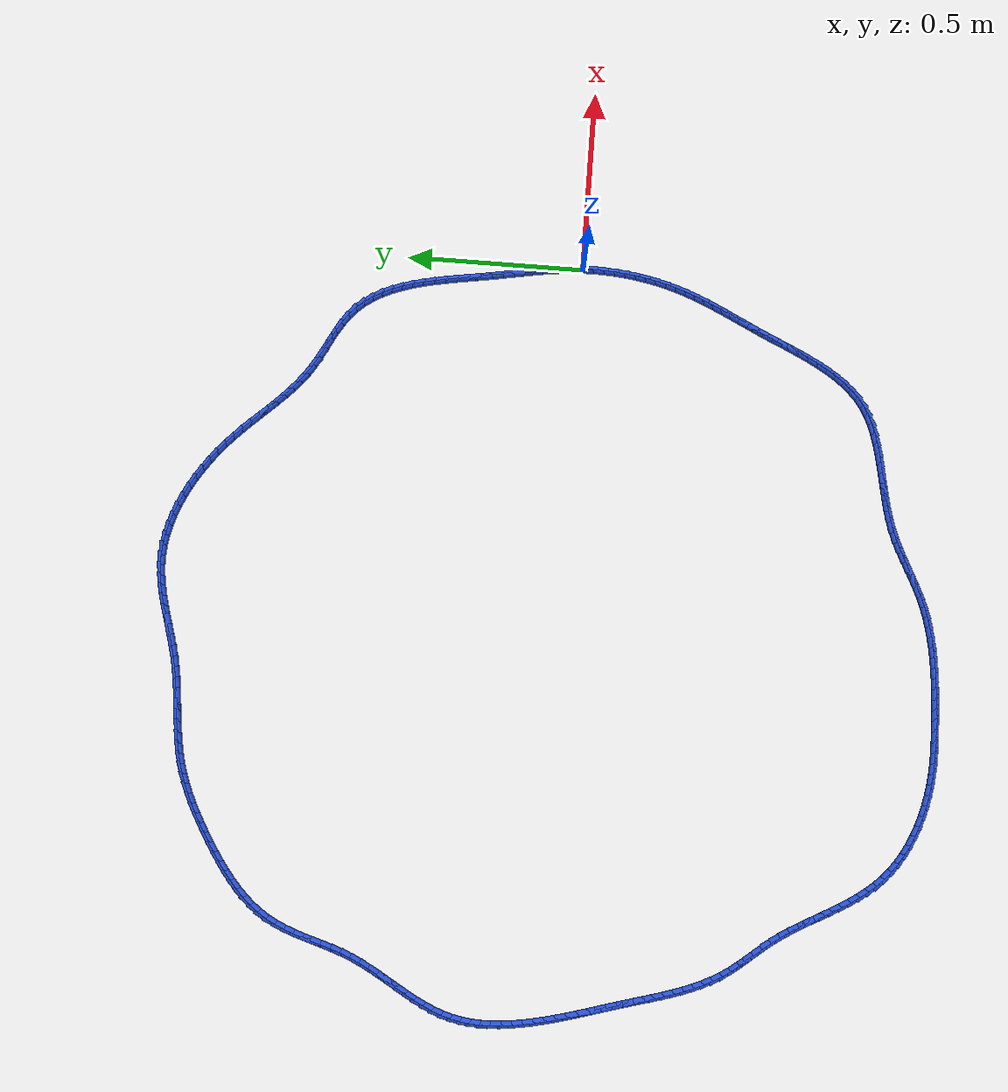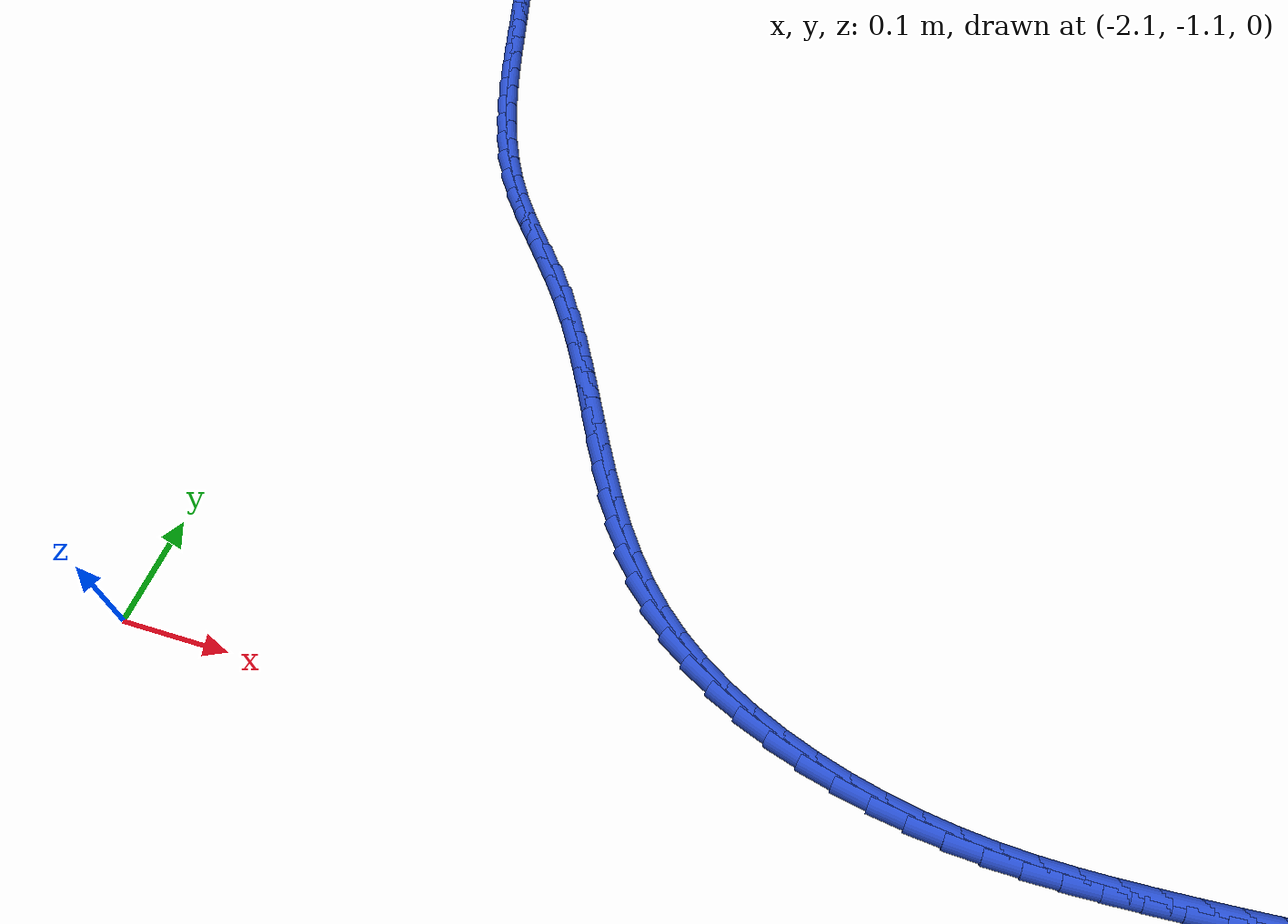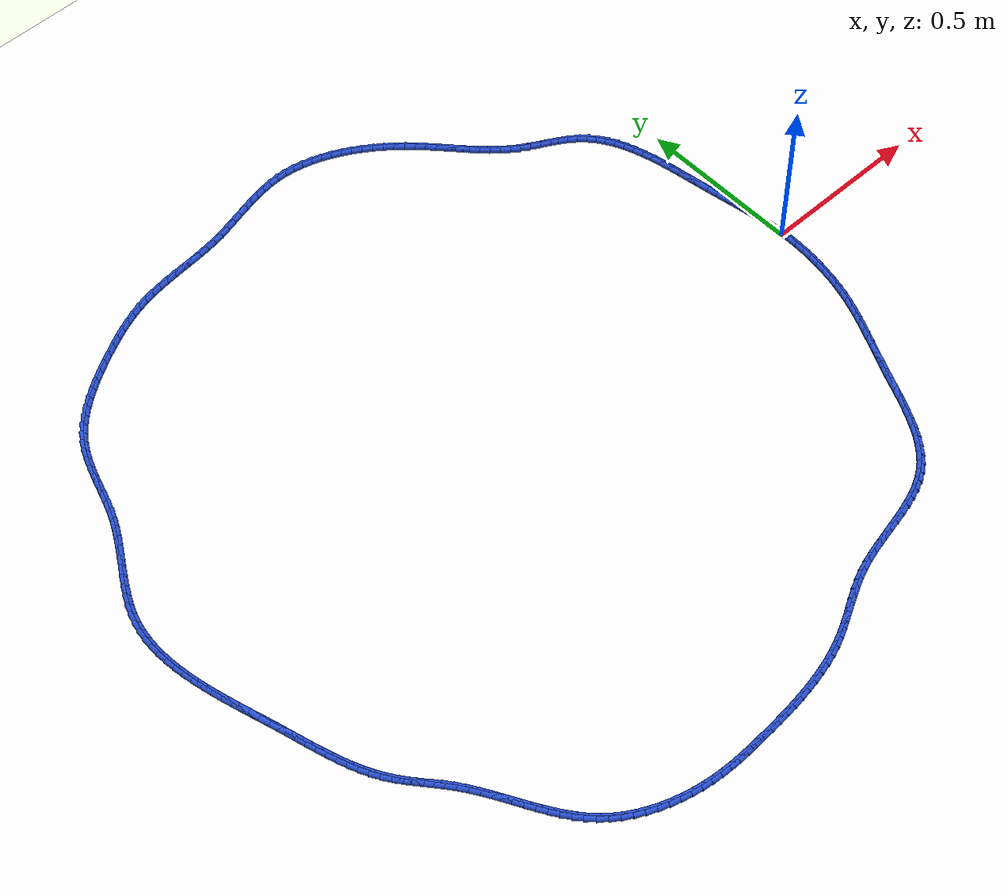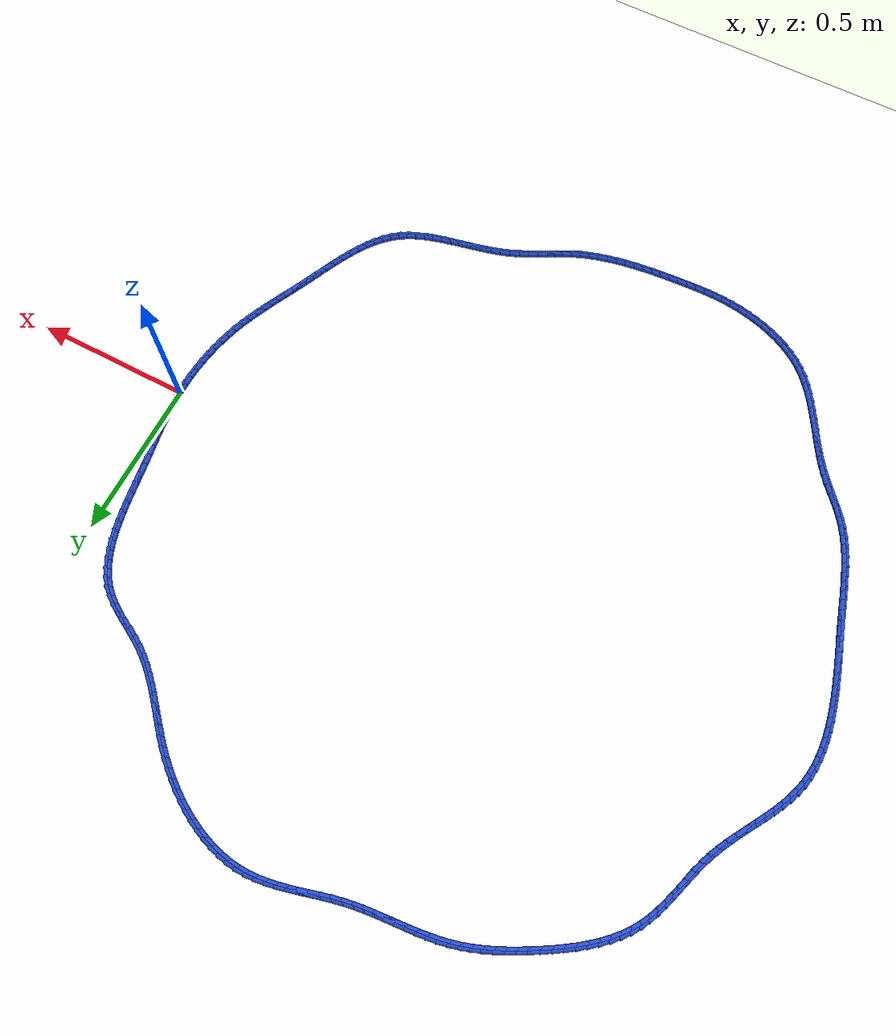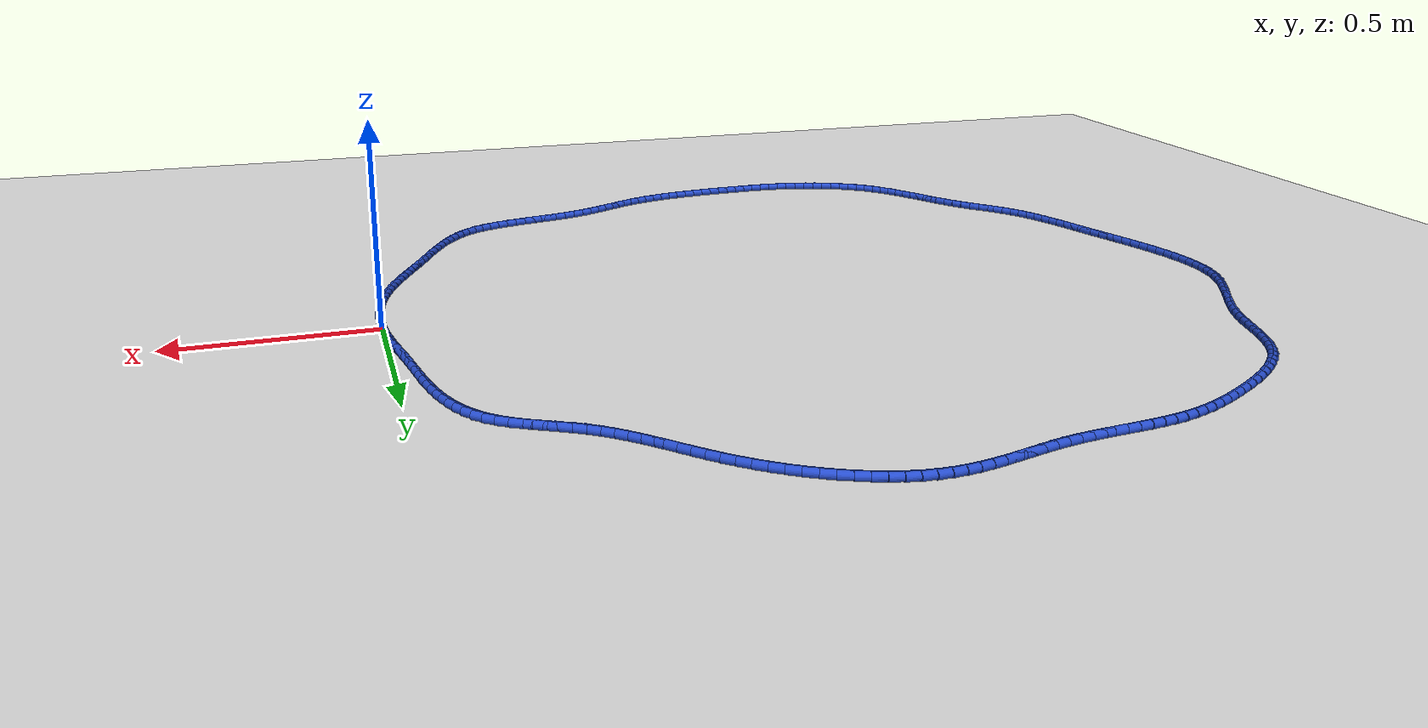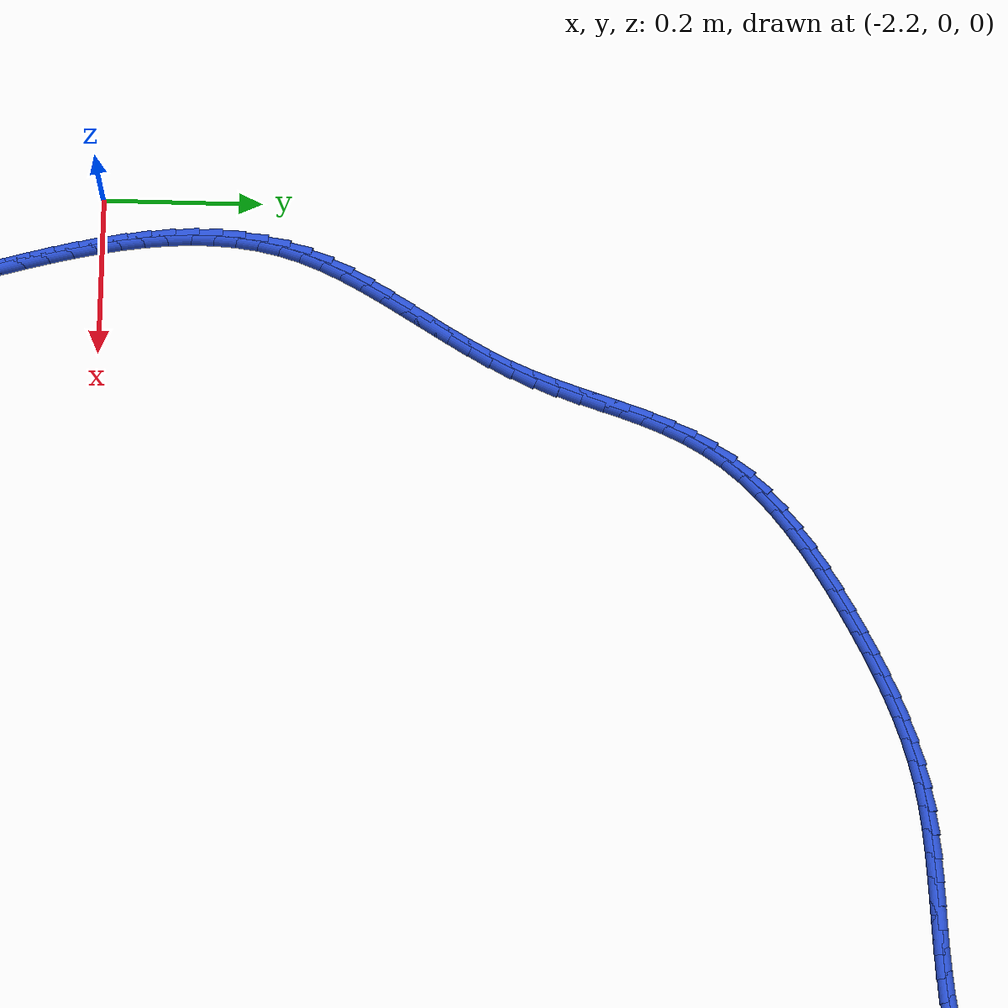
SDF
<sdf version="1.6">
 <world name="default">
  <light name="sun" type="directional">
   <pose>0 0 10 0 -0 0</pose>
   <diffuse>0.8 0.8 0.8 1</diffuse>
   <specular>0.2 0.2 0.2 1</specular>
   <attenuation>
    <range>1000</range>
    <constant>0.9</constant>
    <linear>0.01</linear>
    <quadratic>0.001</quadratic>
   </attenuation>
   <direction>-0.5 0.1 -0.9</direction>
  </light>
  <model name="ground_plane">
   <static>1</static>
   <link name="link">
    <collision name="collision">
     <geometry><plane><normal>0 0 1</normal><size>100 100</size></plane></geometry>
     <surface><friction><ode><mu>100</mu><mu2>50</mu2></ode></friction></surface>
    </collision>
    <visual name="visual">
     <cast_shadows>0</cast_shadows>
     <geometry><plane><normal>0 0 1</normal><size>100 100</size></plane></geometry>
     <material>
      <script><uri>file://media/materials/scripts/gazebo.material</uri><name>Gazebo/WhiteGlow</name></script>
     </material>
    </visual>
   </link>
  </model>
  <gravity>0 0 -9.8</gravity>
  <magnetic_field>6e-06 2.3e-05 -4.2e-05</magnetic_field>
  <atmosphere type="adiabatic"/>
  <physics name="default_physics" default="0" type="ode">
   <max_step_size>0.001</max_step_size>
   <real_time_factor>1</real_time_factor>
   <real_time_update_rate>1000</real_time_update_rate>
  </physics>
  <scene><ambient>0.4 0.4 0.4 1</ambient><background>0.7 0.7 0.7 1</background><shadows>1</shadows></scene>
  <spherical_coordinates>
   <surface_model>EARTH_WGS84</surface_model>
   <latitude_deg>0</latitude_deg>
   <longitude_deg>0</longitude_deg>
   <elevation>0</elevation>
   <heading_deg>0</heading_deg>
  </spherical_coordinates>
  <model name="line">
   <link name="link_0">
    <pose>-1.1275702593849246e-17 6.245004513516506e-17 0.01 0 1.57 -1.518497362297072</pose>
    <collision name="collision">
     <geometry><cylinder><radius>0.01</radius><length>0.08</length></cylinder></geometry>
    </collision>
    <visual name="visual">
     <material>
      <script><name>Gazebo/Blue</name><uri>file://media/materials/scripts/gazebo.material</uri></script>
     </material>
     <geometry><cylinder><radius>0.01</radius><length>0.08</length></cylinder></geometry>
    </visual>
   </link>
   <link name="link_1">
    <pose>-0.0015376829839629721 0.02937497511781898 0.01 0 1.57 -1.484719107940682</pose>
    <collision name="collision">
     <geometry><cylinder><radius>0.01</radius><length>0.08</length></cylinder></geometry>
    </collision>
    <visual name="visual">
     <material>
      <script><name>Gazebo/Blue</name><uri>file://media/materials/scripts/gazebo.material</uri></script>
     </material>
     <geometry><cylinder><radius>0.01</radius><length>0.08</length></cylinder></geometry>
    </visual>
   </link>
   <link name="link_2">
    <pose>-0.004056014433118207 0.05855933687501188 0.01 0 1.57 -1.4562407040690881</pose>
    <collision name="collision">
     <geometry><cylinder><radius>0.01</radius><length>0.08</length></cylinder></geometry>
    </collision>
    <visual name="visual">
     <material>
      <script><name>Gazebo/Blue</name><uri>file://media/materials/scripts/gazebo.material</uri></script>
     </material>
     <geometry><cylinder><radius>0.01</radius><length>0.08</length></cylinder></geometry>
    </visual>
   </link>
   <link name="link_3">
    <pose>-0.0074026261896376925 0.08764529240385857 0.01 0 1.57 -1.4333413156815542</pose>
    <collision name="collision">
     <geometry><cylinder><radius>0.01</radius><length>0.08</length></cylinder></geometry>
    </collision>
    <visual name="visual">
     <material>
      <script><name>Gazebo/Blue</name><uri>file://media/materials/scripts/gazebo.material</uri></script>
     </material>
     <geometry><cylinder><radius>0.01</radius><length>0.08</length></cylinder></geometry>
    </visual>
   </link>
   <link name="link_4">
    <pose>-0.011425150095693374 0.1167250488366388 0.01 0 1.57 -1.4161705437516683</pose>
    <collision name="collision">
     <geometry><cylinder><radius>0.01</radius><length>0.08</length></cylinder></geometry>
    </collision>
    <visual name="visual">
     <material>
      <script><name>Gazebo/Blue</name><uri>file://media/materials/scripts/gazebo.material</uri></script>
     </material>
     <geometry><cylinder><radius>0.01</radius><length>0.08</length></cylinder></geometry>
    </visual>
   </link>
   <link name="link_5">
    <pose>-0.01597121799345723 0.14589081330563233 0.01 0 1.57 -1.4047664375183675</pose>
    <collision name="collision">
     <geometry><cylinder><radius>0.01</radius><length>0.08</length></cylinder></geometry>
    </collision>
    <visual name="visual">
     <material>
      <script><name>Gazebo/Blue</name><uri>file://media/materials/scripts/gazebo.material</uri></script>
     </material>
     <geometry><cylinder><radius>0.01</radius><length>0.08</length></cylinder></geometry>
    </visual>
   </link>
   <link name="link_6">
    <pose>-0.020888461725101223 0.17523479294311897 0.01 0 1.57 -1.3990735710474862</pose>
    <collision name="collision">
     <geometry><cylinder><radius>0.01</radius><length>0.08</length></cylinder></geometry>
    </collision>
    <visual name="visual">
     <material>
      <script><name>Gazebo/Blue</name><uri>file://media/materials/scripts/gazebo.material</uri></script>
     </material>
     <geometry><cylinder><radius>0.01</radius><length>0.08</length></cylinder></geometry>
    </visual>
   </link>
   <link name="link_7">
    <pose>-0.0260245131327973 0.20484919488137837 0.01 0 1.57 -1.3989586597398824</pose>
    <collision name="collision">
     <geometry><cylinder><radius>0.01</radius><length>0.08</length></cylinder></geometry>
    </collision>
    <visual name="visual">
     <material>
      <script><name>Gazebo/Blue</name><uri>file://media/materials/scripts/gazebo.material</uri></script>
     </material>
     <geometry><cylinder><radius>0.01</radius><length>0.08</length></cylinder></geometry>
    </visual>
   </link>
   <link name="link_8">
    <pose>-0.031227004058717433 0.2348262262526903 0.01 0 1.57 -1.4042225320274373</pose>
    <collision name="collision">
     <geometry><cylinder><radius>0.01</radius><length>0.08</length></cylinder></geometry>
    </collision>
    <visual name="visual">
     <material>
      <script><name>Gazebo/Blue</name><uri>file://media/materials/scripts/gazebo.material</uri></script>
     </material>
     <geometry><cylinder><radius>0.01</radius><length>0.08</length></cylinder></geometry>
    </visual>
   </link>
   <link name="link_9">
    <pose>-0.03634356634503359 0.26525809418933466 0.01 0 1.57 -1.4132478607309478</pose>
    <collision name="collision">
     <geometry><cylinder><radius>0.01</radius><length>0.08</length></cylinder></geometry>
    </collision>
    <visual name="visual">
     <material>
      <script><name>Gazebo/Blue</name><uri>file://media/materials/scripts/gazebo.material</uri></script>
     </material>
     <geometry><cylinder><radius>0.01</radius><length>0.08</length></cylinder></geometry>
    </visual>
   </link>
   <link name="link_10">
    <pose>-0.0412600304412104 0.2962055144330096 0.01 0 1.57 -1.41745928508591</pose>
    <collision name="collision">
     <geometry><cylinder><radius>0.01</radius><length>0.08</length></cylinder></geometry>
    </collision>
    <visual name="visual">
     <material>
      <script><name>Gazebo/Blue</name><uri>file://media/materials/scripts/gazebo.material</uri></script>
     </material>
     <geometry><cylinder><radius>0.01</radius><length>0.08</length></cylinder></geometry>
    </visual>
   </link>
   <link name="link_11">
    <pose>-0.04610153267686795 0.32753191608397536 0.01 0 1.57 -1.4138339207160273</pose>
    <collision name="collision">
     <geometry><cylinder><radius>0.01</radius><length>0.08</length></cylinder></geometry>
    </collision>
    <visual name="visual">
     <material>
      <script><name>Gazebo/Blue</name><uri>file://media/materials/scripts/gazebo.material</uri></script>
     </material>
     <geometry><cylinder><radius>0.01</radius><length>0.08</length></cylinder></geometry>
    </visual>
   </link>
   <link name="link_12">
    <pose>-0.051085682434906014 0.35902449234685363 0.01 0 1.57 -1.4024425547172414</pose>
    <collision name="collision">
     <geometry><cylinder><radius>0.01</radius><length>0.08</length></cylinder></geometry>
    </collision>
    <visual name="visual">
     <material>
      <script><name>Gazebo/Blue</name><uri>file://media/materials/scripts/gazebo.material</uri></script>
     </material>
     <geometry><cylinder><radius>0.01</radius><length>0.08</length></cylinder></geometry>
    </visual>
   </link>
   <link name="link_13">
    <pose>-0.056430287856641524 0.39047027256744016 0.01 0 1.57 -1.3831109274437807</pose>
    <collision name="collision">
     <geometry><cylinder><radius>0.01</radius><length>0.08</length></cylinder></geometry>
    </collision>
    <visual name="visual">
     <material>
      <script><name>Gazebo/Blue</name><uri>file://media/materials/scripts/gazebo.material</uri></script>
     </material>
     <geometry><cylinder><radius>0.01</radius><length>0.08</length></cylinder></geometry>
    </visual>
   </link>
   <link name="link_14">
    <pose>-0.06235315708339143 0.42165628609153105 0.01 0 1.57 -1.355425825009673</pose>
    <collision name="collision">
     <geometry><cylinder><radius>0.01</radius><length>0.08</length></cylinder></geometry>
    </collision>
    <visual name="visual">
     <material>
      <script><name>Gazebo/Blue</name><uri>file://media/materials/scripts/gazebo.material</uri></script>
     </material>
     <geometry><cylinder><radius>0.01</radius><length>0.08</length></cylinder></geometry>
    </visual>
   </link>
   <link name="link_15">
    <pose>-0.0690720982564727 0.45236956226492214 0.01 0 1.57 -1.3187488280029438</pose>
    <collision name="collision">
     <geometry><cylinder><radius>0.01</radius><length>0.08</length></cylinder></geometry>
    </collision>
    <visual name="visual">
     <material>
      <script><name>Gazebo/Blue</name><uri>file://media/materials/scripts/gazebo.material</uri></script>
     </material>
     <geometry><cylinder><radius>0.01</radius><length>0.08</length></cylinder></geometry>
    </visual>
   </link>
   <link name="link_16">
    <pose>-0.07680491951720222 0.48239713043340926 0.01 0 1.57 -1.2722417535709725</pose>
    <collision name="collision">
     <geometry><cylinder><radius>0.01</radius><length>0.08</length></cylinder></geometry>
    </collision>
    <visual name="visual">
     <material>
      <script><name>Gazebo/Blue</name><uri>file://media/materials/scripts/gazebo.material</uri></script>
     </material>
     <geometry><cylinder><radius>0.01</radius><length>0.08</length></cylinder></geometry>
    </visual>
   </link>
   <link name="link_17">
    <pose>-0.08576942900689699 0.5115260199427882 0.01 0 1.57 -1.2149220141728678</pose>
    <collision name="collision">
     <geometry><cylinder><radius>0.01</radius><length>0.08</length></cylinder></geometry>
    </collision>
    <visual name="visual">
     <material>
      <script><name>Gazebo/Blue</name><uri>file://media/materials/scripts/gazebo.material</uri></script>
     </material>
     <geometry><cylinder><radius>0.01</radius><length>0.08</length></cylinder></geometry>
    </visual>
   </link>
   <link name="link_18">
    <pose>-0.09618343486687392 0.539543260138855 0.01 0 1.57 -1.1457751777536347</pose>
    <collision name="collision">
     <geometry><cylinder><radius>0.01</radius><length>0.08</length></cylinder></geometry>
    </collision>
    <visual name="visual">
     <material>
      <script><name>Gazebo/Blue</name><uri>file://media/materials/scripts/gazebo.material</uri></script>
     </material>
     <geometry><cylinder><radius>0.01</radius><length>0.08</length></cylinder></geometry>
    </visual>
   </link>
   <link name="link_19">
    <pose>-0.10826474523844995 0.5662358803674054 0.01 0 1.57 -1.0639589083681769</pose>
    <collision name="collision">
     <geometry><cylinder><radius>0.01</radius><length>0.08</length></cylinder></geometry>
    </collision>
    <visual name="visual">
     <material>
      <script><name>Gazebo/Blue</name><uri>file://media/materials/scripts/gazebo.material</uri></script>
     </material>
     <geometry><cylinder><radius>0.01</radius><length>0.08</length></cylinder></geometry>
    </visual>
   </link>
   <link name="link_20">
    <pose>-0.12223116826294202 0.5913909099742352 0.01 0 1.57 -0.9691251442633072</pose>
    <collision name="collision">
     <geometry><cylinder><radius>0.01</radius><length>0.08</length></cylinder></geometry>
    </collision>
    <visual name="visual">
     <material>
      <script><name>Gazebo/Blue</name><uri>file://media/materials/scripts/gazebo.material</uri></script>
     </material>
     <geometry><cylinder><radius>0.01</radius><length>0.08</length></cylinder></geometry>
    </visual>
   </link>
   <link name="link_21">
    <pose>-0.1383005120816671 0.6147953783051404 0.01 0 1.57 -0.8618440866413085</pose>
    <collision name="collision">
     <geometry><cylinder><radius>0.01</radius><length>0.08</length></cylinder></geometry>
    </collision>
    <visual name="visual">
     <material>
      <script><name>Gazebo/Blue</name><uri>file://media/materials/scripts/gazebo.material</uri></script>
     </material>
     <geometry><cylinder><radius>0.01</radius><length>0.08</length></cylinder></geometry>
    </visual>
   </link>
   <link name="link_22">
    <pose>-0.1566905848359421 0.6362363147059168 0.01 0 1.57 -0.7443963743628462</pose>
    <collision name="collision">
     <geometry><cylinder><radius>0.01</radius><length>0.08</length></cylinder></geometry>
    </collision>
    <visual name="visual">
     <material>
      <script><name>Gazebo/Blue</name><uri>file://media/materials/scripts/gazebo.material</uri></script>
     </material>
     <geometry><cylinder><radius>0.01</radius><length>0.08</length></cylinder></geometry>
    </visual>
   </link>
   <link name="link_23">
    <pose>-0.17761126916861394 0.65550811130373 0.01 0 1.57 -0.6364197757738635</pose>
    <collision name="collision">
     <geometry><cylinder><radius>0.01</radius><length>0.08</length></cylinder></geometry>
    </collision>
    <visual name="visual">
     <material>
      <script><name>Gazebo/Blue</name><uri>file://media/materials/scripts/gazebo.material</uri></script>
     </material>
     <geometry><cylinder><radius>0.01</radius><length>0.08</length></cylinder></geometry>
    </visual>
   </link>
   <link name="link_24">
    <pose>-0.2009196808169959 0.6727328803823608 0.01 0 1.57 -0.561010420184418</pose>
    <collision name="collision">
     <geometry><cylinder><radius>0.01</radius><length>0.08</length></cylinder></geometry>
    </collision>
    <visual name="visual">
     <material>
      <script><name>Gazebo/Blue</name><uri>file://media/materials/scripts/gazebo.material</uri></script>
     </material>
     <geometry><cylinder><radius>0.01</radius><length>0.08</length></cylinder></geometry>
    </visual>
   </link>
   <link name="link_25">
    <pose>-0.22598702359330816 0.6884841459926657 0.01 0 1.57 -0.5172548308809158</pose>
    <collision name="collision">
     <geometry><cylinder><radius>0.01</radius><length>0.08</length></cylinder></geometry>
    </collision>
    <visual name="visual">
     <material>
      <script><name>Gazebo/Blue</name><uri>file://media/materials/scripts/gazebo.material</uri></script>
     </material>
     <geometry><cylinder><radius>0.01</radius><length>0.08</length></cylinder></geometry>
    </visual>
   </link>
   <link name="link_26">
    <pose>-0.2521490878858158 0.7033683312263781 0.01 0 1.57 -0.5027742366577302</pose>
    <collision name="collision">
     <geometry><cylinder><radius>0.01</radius><length>0.08</length></cylinder></geometry>
    </collision>
    <visual name="visual">
     <material>
      <script><name>Gazebo/Blue</name><uri>file://media/materials/scripts/gazebo.material</uri></script>
     </material>
     <geometry><cylinder><radius>0.01</radius><length>0.08</length></cylinder></geometry>
    </visual>
   </link>
   <link name="link_27">
    <pose>-0.2787416640827836 0.7179918591752307 0.01 0 1.57 -0.516484557182896</pose>
    <collision name="collision">
     <geometry><cylinder><radius>0.01</radius><length>0.08</length></cylinder></geometry>
    </collision>
    <visual name="visual">
     <material>
      <script><name>Gazebo/Blue</name><uri>file://media/materials/scripts/gazebo.material</uri></script>
     </material>
     <geometry><cylinder><radius>0.01</radius><length>0.08</length></cylinder></geometry>
    </visual>
   </link>
   <link name="link_28">
    <pose>-0.30510054257247665 0.7329611529309566 0.01 0 1.57 -0.5588358367193917</pose>
    <collision name="collision">
     <geometry><cylinder><radius>0.01</radius><length>0.08</length></cylinder></geometry>
    </collision>
    <visual name="visual">
     <material>
      <script><name>Gazebo/Blue</name><uri>file://media/materials/scripts/gazebo.material</uri></script>
     </material>
     <geometry><cylinder><radius>0.01</radius><length>0.08</length></cylinder></geometry>
    </visual>
   </link>
   <link name="link_29">
    <pose>-0.33056151374428183 0.7488826355842866 0.01 0 1.57 -0.6247029955184475</pose>
    <collision name="collision">
     <geometry><cylinder><radius>0.01</radius><length>0.08</length></cylinder></geometry>
    </collision>
    <visual name="visual">
     <material>
      <script><name>Gazebo/Blue</name><uri>file://media/materials/scripts/gazebo.material</uri></script>
     </material>
     <geometry><cylinder><radius>0.01</radius><length>0.08</length></cylinder></geometry>
    </visual>
   </link>
   <link name="link_30">
    <pose>-0.3546141539956103 0.7662253812732389 0.01 0 1.57 -0.687753033432235</pose>
    <collision name="collision">
     <geometry><cylinder><radius>0.01</radius><length>0.08</length></cylinder></geometry>
    </collision>
    <visual name="visual">
     <material>
      <script><name>Gazebo/Blue</name><uri>file://media/materials/scripts/gazebo.material</uri></script>
     </material>
     <geometry><cylinder><radius>0.01</radius><length>0.08</length></cylinder></geometry>
    </visual>
   </link>
   <link name="link_31">
    <pose>-0.37735960770271954 0.7849122621601992 0.01 0 1.57 -0.7402997913277448</pose>
    <collision name="collision">
     <geometry><cylinder><radius>0.01</radius><length>0.08</length></cylinder></geometry>
    </collision>
    <visual name="visual">
     <material>
      <script><name>Gazebo/Blue</name><uri>file://media/materials/scripts/gazebo.material</uri></script>
     </material>
     <geometry><cylinder><radius>0.01</radius><length>0.08</length></cylinder></geometry>
    </visual>
   </link>
   <link name="link_32">
    <pose>-0.39905102241437884 0.8047303937361787 0.01 0 1.57 -0.7816980474084336</pose>
    <collision name="collision">
     <geometry><cylinder><radius>0.01</radius><length>0.08</length></cylinder></geometry>
    </collision>
    <visual name="visual">
     <material>
      <script><name>Gazebo/Blue</name><uri>file://media/materials/scripts/gazebo.material</uri></script>
     </material>
     <geometry><cylinder><radius>0.01</radius><length>0.08</length></cylinder></geometry>
    </visual>
   </link>
   <link name="link_33">
    <pose>-0.4199415456793574 0.825466891492188 0.01 0 1.57 -0.8116983417721163</pose>
    <collision name="collision">
     <geometry><cylinder><radius>0.01</radius><length>0.08</length></cylinder></geometry>
    </collision>
    <visual name="visual">
     <material>
      <script><name>Gazebo/Blue</name><uri>file://media/materials/scripts/gazebo.material</uri></script>
     </material>
     <geometry><cylinder><radius>0.01</radius><length>0.08</length></cylinder></geometry>
    </visual>
   </link>
   <link name="link_34">
    <pose>-0.440284325046424 0.8469088709192376 0.01 0 1.57 -0.8303005381225971</pose>
    <collision name="collision">
     <geometry><cylinder><radius>0.01</radius><length>0.08</length></cylinder></geometry>
    </collision>
    <visual name="visual">
     <material>
      <script><name>Gazebo/Blue</name><uri>file://media/materials/scripts/gazebo.material</uri></script>
     </material>
     <geometry><cylinder><radius>0.01</radius><length>0.08</length></cylinder></geometry>
    </visual>
   </link>
   <link name="link_35">
    <pose>-0.46033250806434794 0.8688434475083382 0.01 0 1.57 -0.8376362777605216</pose>
    <collision name="collision">
     <geometry><cylinder><radius>0.01</radius><length>0.08</length></cylinder></geometry>
    </collision>
    <visual name="visual">
     <material>
      <script><name>Gazebo/Blue</name><uri>file://media/materials/scripts/gazebo.material</uri></script>
     </material>
     <geometry><cylinder><radius>0.01</radius><length>0.08</length></cylinder></geometry>
    </visual>
   </link>
   <link name="link_36">
    <pose>-0.4803392422818983 0.8910577367505006 0.01 0 1.57 -0.8338943730259506</pose>
    <collision name="collision">
     <geometry><cylinder><radius>0.01</radius><length>0.08</length></cylinder></geometry>
    </collision>
    <visual name="visual">
     <material>
      <script><name>Gazebo/Blue</name><uri>file://media/materials/scripts/gazebo.material</uri></script>
     </material>
     <geometry><cylinder><radius>0.01</radius><length>0.08</length></cylinder></geometry>
    </visual>
   </link>
   <link name="link_37">
    <pose>-0.5005576752478441 0.9133388541367353 0.01 0 1.57 -0.8192907854374705</pose>
    <collision name="collision">
     <geometry><cylinder><radius>0.01</radius><length>0.08</length></cylinder></geometry>
    </collision>
    <visual name="visual">
     <material>
      <script><name>Gazebo/Blue</name><uri>file://media/materials/scripts/gazebo.material</uri></script>
     </material>
     <geometry><cylinder><radius>0.01</radius><length>0.08</length></cylinder></geometry>
    </visual>
   </link>
   <link name="link_38">
    <pose>-0.5212409545109543 0.9354739151580536 0.01 0 1.57 -0.7940795031723882</pose>
    <collision name="collision">
     <geometry><cylinder><radius>0.01</radius><length>0.08</length></cylinder></geometry>
    </collision>
    <visual name="visual">
     <material>
      <script><name>Gazebo/Blue</name><uri>file://media/materials/scripts/gazebo.material</uri></script>
     </material>
     <geometry><cylinder><radius>0.01</radius><length>0.08</length></cylinder></geometry>
    </visual>
   </link>
   <link name="link_39">
    <pose>-0.5426422276199983 0.9572500353054652 0.01 0 1.57 -0.7589108666392237</pose>
    <collision name="collision">
     <geometry><cylinder><radius>0.01</radius><length>0.08</length></cylinder></geometry>
    </collision>
    <visual name="visual">
     <material>
      <script><name>Gazebo/Blue</name><uri>file://media/materials/scripts/gazebo.material</uri></script>
     </material>
     <geometry><cylinder><radius>0.01</radius><length>0.08</length></cylinder></geometry>
    </visual>
   </link>
   <link name="link_40">
    <pose>-0.5650031727831223 0.9784567217351604 0.01 0 1.57 -0.7189424117038082</pose>
    <collision name="collision">
     <geometry><cylinder><radius>0.01</radius><length>0.08</length></cylinder></geometry>
    </collision>
    <visual name="visual">
     <material>
      <script><name>Gazebo/Blue</name><uri>file://media/materials/scripts/gazebo.material</uri></script>
     </material>
     <geometry><cylinder><radius>0.01</radius><length>0.08</length></cylinder></geometry>
    </visual>
   </link>
   <link name="link_41">
    <pose>-0.5883856018967509 0.9989209885541362 0.01 0 1.57 -0.6777496393009657</pose>
    <collision name="collision">
     <geometry><cylinder><radius>0.01</radius><length>0.08</length></cylinder></geometry>
    </collision>
    <visual name="visual">
     <material>
      <script><name>Gazebo/Blue</name><uri>file://media/materials/scripts/gazebo.material</uri></script>
     </material>
     <geometry><cylinder><radius>0.01</radius><length>0.08</length></cylinder></geometry>
    </visual>
   </link>
   <link name="link_42">
    <pose>-0.6127085202759879 1.0184996288723043 0.01 0 1.57 -0.6349768824526923</pose>
    <collision name="collision">
     <geometry><cylinder><radius>0.01</radius><length>0.08</length></cylinder></geometry>
    </collision>
    <visual name="visual">
     <material>
      <script><name>Gazebo/Blue</name><uri>file://media/materials/scripts/gazebo.material</uri></script>
     </material>
     <geometry><cylinder><radius>0.01</radius><length>0.08</length></cylinder></geometry>
    </visual>
   </link>
   <link name="link_43">
    <pose>-0.6378869997466092 1.0370502560376138 0.01 0 1.57 -0.5901557132650499</pose>
    <collision name="collision">
     <geometry><cylinder><radius>0.01</radius><length>0.08</length></cylinder></geometry>
    </collision>
    <visual name="visual">
     <material>
      <script><name>Gazebo/Blue</name><uri>file://media/materials/scripts/gazebo.material</uri></script>
     </material>
     <geometry><cylinder><radius>0.01</radius><length>0.08</length></cylinder></geometry>
    </visual>
   </link>
   <link name="link_44">
    <pose>-0.663836112134391 1.0544304833980143 0.01 0 1.57 -0.5428054351767756</pose>
    <collision name="collision">
     <geometry><cylinder><radius>0.01</radius><length>0.08</length></cylinder></geometry>
    </collision>
    <visual name="visual">
     <material>
      <script><name>Gazebo/Blue</name><uri>file://media/materials/scripts/gazebo.material</uri></script>
     </material>
     <geometry><cylinder><radius>0.01</radius><length>0.08</length></cylinder></geometry>
    </visual>
   </link>
   <link name="link_45">
    <pose>-0.6904709292651088 1.0704979243014552 0.01 0 1.57 -0.4924300811574573</pose>
    <collision name="collision">
     <geometry><cylinder><radius>0.01</radius><length>0.08</length></cylinder></geometry>
    </collision>
    <visual name="visual">
     <material>
      <script><name>Gazebo/Blue</name><uri>file://media/materials/scripts/gazebo.material</uri></script>
     </material>
     <geometry><cylinder><radius>0.01</radius><length>0.08</length></cylinder></geometry>
    </visual>
   </link>
   <link name="link_46">
    <pose>-0.7177065229645391 1.085110192095886 0.01 0 1.57 -0.4385202871380731</pose>
    <collision name="collision">
     <geometry><cylinder><radius>0.01</radius><length>0.08</length></cylinder></geometry>
    </collision>
    <visual name="visual">
     <material>
      <script><name>Gazebo/Blue</name><uri>file://media/materials/scripts/gazebo.material</uri></script>
     </material>
     <geometry><cylinder><radius>0.01</radius><length>0.08</length></cylinder></geometry>
    </visual>
   </link>
   <link name="link_47">
    <pose>-0.7454579650584574 1.0981249001292563 0.01 0 1.57 -0.3805619466630048</pose>
    <collision name="collision">
     <geometry><cylinder><radius>0.01</radius><length>0.08</length></cylinder></geometry>
    </collision>
    <visual name="visual">
     <material>
      <script><name>Gazebo/Blue</name><uri>file://media/materials/scripts/gazebo.material</uri></script>
     </material>
     <geometry><cylinder><radius>0.01</radius><length>0.08</length></cylinder></geometry>
    </visual>
   </link>
   <link name="link_48">
    <pose>-0.7736403273726403 1.1093996617495159 0.01 0 1.57 -0.3180542355107313</pose>
    <collision name="collision">
     <geometry><cylinder><radius>0.01</radius><length>0.08</length></cylinder></geometry>
    </collision>
    <visual name="visual">
     <material>
      <script><name>Gazebo/Blue</name><uri>file://media/materials/scripts/gazebo.material</uri></script>
     </material>
     <geometry><cylinder><radius>0.01</radius><length>0.08</length></cylinder></geometry>
    </visual>
   </link>
   <link name="link_49">
    <pose>-0.8021686817328633 1.118792090304614 0.01 0 1.57 -0.25054004220195664</pose>
    <collision name="collision">
     <geometry><cylinder><radius>0.01</radius><length>0.08</length></cylinder></geometry>
    </collision>
    <visual name="visual">
     <material>
      <script><name>Gazebo/Blue</name><uri>file://media/materials/scripts/gazebo.material</uri></script>
     </material>
     <geometry><cylinder><radius>0.01</radius><length>0.08</length></cylinder></geometry>
    </visual>
   </link>
   <link name="link_50">
    <pose>-0.8309580999649026 1.1261597991425 0.01 0 1.57 -0.17765158357711866</pose>
    <collision name="collision">
     <geometry><cylinder><radius>0.01</radius><length>0.08</length></cylinder></geometry>
    </collision>
    <visual name="visual">
     <material>
      <script><name>Gazebo/Blue</name><uri>file://media/materials/scripts/gazebo.material</uri></script>
     </material>
     <geometry><cylinder><radius>0.01</radius><length>0.08</length></cylinder></geometry>
    </visual>
   </link>
   <link name="link_51">
    <pose>-0.8599236538945341 1.1313604016111234 0.01 0 1.57 -0.09917227274156644</pose>
    <collision name="collision">
     <geometry><cylinder><radius>0.01</radius><length>0.08</length></cylinder></geometry>
    </collision>
    <visual name="visual">
     <material>
      <script><name>Gazebo/Blue</name><uri>file://media/materials/scripts/gazebo.material</uri></script>
     </material>
     <geometry><cylinder><radius>0.01</radius><length>0.08</length></cylinder></geometry>
    </visual>
   </link>
   <link name="link_52">
    <pose>-0.8889804153475342 1.1342515110584346 0.01 0 1.57 -0.01524505226586044</pose>
    <collision name="collision">
     <geometry><cylinder><radius>0.01</radius><length>0.08</length></cylinder></geometry>
    </collision>
    <visual name="visual">
     <material>
      <script><name>Gazebo/Blue</name><uri>file://media/materials/scripts/gazebo.material</uri></script>
     </material>
     <geometry><cylinder><radius>0.01</radius><length>0.08</length></cylinder></geometry>
    </visual>
   </link>
   <link name="link_53">
    <pose>-0.9180442202745205 1.1346946246123693 0.01 0 1.57 0.06656141050745533</pose>
    <collision name="collision">
     <geometry><cylinder><radius>0.01</radius><length>0.08</length></cylinder></geometry>
    </collision>
    <visual name="visual">
     <material>
      <script><name>Gazebo/Blue</name><uri>file://media/materials/scripts/gazebo.material</uri></script>
     </material>
     <geometry><cylinder><radius>0.01</radius><length>0.08</length></cylinder></geometry>
    </visual>
   </link>
   <link name="link_54">
    <pose>-0.9470719074345628 1.1327596423712916 0.01 0 1.57 0.1347747029561479</pose>
    <collision name="collision">
     <geometry><cylinder><radius>0.01</radius><length>0.08</length></cylinder></geometry>
    </collision>
    <visual name="visual">
     <material>
      <script><name>Gazebo/Blue</name><uri>file://media/materials/scripts/gazebo.material</uri></script>
     </material>
     <geometry><cylinder><radius>0.01</radius><length>0.08</length></cylinder></geometry>
    </visual>
   </link>
   <link name="link_55">
    <pose>-0.9760812305306704 1.128826073841794 0.01 0 1.57 0.18825842575632595</pose>
    <collision name="collision">
     <geometry><cylinder><radius>0.01</radius><length>0.08</length></cylinder></geometry>
    </collision>
    <visual name="visual">
     <material>
      <script><name>Gazebo/Blue</name><uri>file://media/materials/scripts/gazebo.material</uri></script>
     </material>
     <geometry><cylinder><radius>0.01</radius><length>0.08</length></cylinder></geometry>
    </visual>
   </link>
   <link name="link_56">
    <pose>-1.0050948864708935 1.1232985531171273 0.01 0 1.57 0.2272938388361072</pose>
    <collision name="collision">
     <geometry><cylinder><radius>0.01</radius><length>0.08</length></cylinder></geometry>
    </collision>
    <visual name="visual">
     <material>
      <script><name>Gazebo/Blue</name><uri>file://media/materials/scripts/gazebo.material</uri></script>
     </material>
     <geometry><cylinder><radius>0.01</radius><length>0.08</length></cylinder></geometry>
    </visual>
   </link>
   <link name="link_57">
    <pose>-1.0341355721632826 1.1165817142905419 0.01 0 1.57 0.2523711938627876</pose>
    <collision name="collision">
     <geometry><cylinder><radius>0.01</radius><length>0.08</length></cylinder></geometry>
    </collision>
    <visual name="visual">
     <material>
      <script><name>Gazebo/Blue</name><uri>file://media/materials/scripts/gazebo.material</uri></script>
     </material>
     <geometry><cylinder><radius>0.01</radius><length>0.08</length></cylinder></geometry>
    </visual>
   </link>
   <link name="link_58">
    <pose>-1.0632259845158893 1.1090801914552888 0.01 0 1.57 0.2639549422499165</pose>
    <collision name="collision">
     <geometry><cylinder><radius>0.01</radius><length>0.08</length></cylinder></geometry>
    </collision>
    <visual name="visual">
     <material>
      <script><name>Gazebo/Blue</name><uri>file://media/materials/scripts/gazebo.material</uri></script>
     </material>
     <geometry><cylinder><radius>0.01</radius><length>0.08</length></cylinder></geometry>
    </visual>
   </link>
   <link name="link_59">
    <pose>-1.0923888204367642 1.1011986187046174 0.01 0 1.57 0.26235235323605666</pose>
    <collision name="collision">
     <geometry><cylinder><radius>0.01</radius><length>0.08</length></cylinder></geometry>
    </collision>
    <visual name="visual">
     <material>
      <script><name>Gazebo/Blue</name><uri>file://media/materials/scripts/gazebo.material</uri></script>
     </material>
     <geometry><cylinder><radius>0.01</radius><length>0.08</length></cylinder></geometry>
    </visual>
   </link>
   <link name="link_60">
    <pose>-1.1216467768339575 1.0933416301317795 0.01 0 1.57 0.24766260051235447</pose>
    <collision name="collision">
     <geometry><cylinder><radius>0.01</radius><length>0.08</length></cylinder></geometry>
    </collision>
    <visual name="visual">
     <material>
      <script><name>Gazebo/Blue</name><uri>file://media/materials/scripts/gazebo.material</uri></script>
     </material>
     <geometry><cylinder><radius>0.01</radius><length>0.08</length></cylinder></geometry>
    </visual>
   </link>
   <link name="link_61">
    <pose>-1.1510225506155207 1.0859138598300249 0.01 0 1.57 0.21979034669728906</pose>
    <collision name="collision">
     <geometry><cylinder><radius>0.01</radius><length>0.08</length></cylinder></geometry>
    </collision>
    <visual name="visual">
     <material>
      <script><name>Gazebo/Blue</name><uri>file://media/materials/scripts/gazebo.material</uri></script>
     </material>
     <geometry><cylinder><radius>0.01</radius><length>0.08</length></cylinder></geometry>
    </visual>
   </link>
   <link name="link_62">
    <pose>-1.1805388386895042 1.0793199418926047 0.01 0 1.57 0.1802586437197359</pose>
    <collision name="collision">
     <geometry><cylinder><radius>0.01</radius><length>0.08</length></cylinder></geometry>
    </collision>
    <visual name="visual">
     <material>
      <script><name>Gazebo/Blue</name><uri>file://media/materials/scripts/gazebo.material</uri></script>
     </material>
     <geometry><cylinder><radius>0.01</radius><length>0.08</length></cylinder></geometry>
    </visual>
   </link>
   <link name="link_63">
    <pose>-1.2102122684973604 1.073912352489335 0.01 0 1.57 0.1434360916557586</pose>
    <collision name="collision">
     <geometry><cylinder><radius>0.01</radius><length>0.08</length></cylinder></geometry>
    </collision>
    <visual name="visual">
     <material>
      <script><name>Gazebo/Blue</name><uri>file://media/materials/scripts/gazebo.material</uri></script>
     </material>
     <geometry><cylinder><radius>0.01</radius><length>0.08</length></cylinder></geometry>
    </visual>
   </link>
   <link name="link_64">
    <pose>-1.2400088851289501 1.0696088886665351 0.01 0 1.57 0.11659366766979566</pose>
    <collision name="collision">
     <geometry><cylinder><radius>0.01</radius><length>0.08</length></cylinder></geometry>
    </collision>
    <visual name="visual">
     <material>
      <script><name>Gazebo/Blue</name><uri>file://media/materials/scripts/gazebo.material</uri></script>
     </material>
     <geometry><cylinder><radius>0.01</radius><length>0.08</length></cylinder></geometry>
    </visual>
   </link>
   <link name="link_65">
    <pose>-1.2698696108476741 1.0661114546177148 0.01 0 1.57 0.09981794766095574</pose>
    <collision name="collision">
     <geometry><cylinder><radius>0.01</radius><length>0.08</length></cylinder></geometry>
    </collision>
    <visual name="visual">
     <material>
      <script><name>Gazebo/Blue</name><uri>file://media/materials/scripts/gazebo.material</uri></script>
     </material>
     <geometry><cylinder><radius>0.01</radius><length>0.08</length></cylinder></geometry>
    </visual>
   </link>
   <link name="link_66">
    <pose>-1.2997351862791553 1.0631203936332825 0.01 0 1.57 0.09312921225657378</pose>
    <collision name="collision">
     <geometry><cylinder><radius>0.01</radius><length>0.08</length></cylinder></geometry>
    </collision>
    <visual name="visual">
     <material>
      <script><name>Gazebo/Blue</name><uri>file://media/materials/scripts/gazebo.material</uri></script>
     </material>
     <geometry><cylinder><radius>0.01</radius><length>0.08</length></cylinder></geometry>
    </visual>
   </link>
   <link name="link_67">
    <pose>-1.3295463520490158 1.0603360490036464 0.01 0 1.57 0.0965849872808206</pose>
    <collision name="collision">
     <geometry><cylinder><radius>0.01</radius><length>0.08</length></cylinder></geometry>
    </collision>
    <visual name="visual">
     <material>
      <script><name>Gazebo/Blue</name><uri>file://media/materials/scripts/gazebo.material</uri></script>
     </material>
     <geometry><cylinder><radius>0.01</radius><length>0.08</length></cylinder></geometry>
    </visual>
   </link>
   <link name="link_68">
    <pose>-1.3592438487828804 1.0574587640192152 0.01 0 1.57 0.11030170786237654</pose>
    <collision name="collision">
     <geometry><cylinder><radius>0.01</radius><length>0.08</length></cylinder></geometry>
    </collision>
    <visual name="visual">
     <material>
      <script><name>Gazebo/Blue</name><uri>file://media/materials/scripts/gazebo.material</uri></script>
     </material>
     <geometry><cylinder><radius>0.01</radius><length>0.08</length></cylinder></geometry>
    </visual>
   </link>
   <link name="link_69">
    <pose>-1.388768417106371 1.054188881970397 0.01 0 1.57 0.13444568912209892</pose>
    <collision name="collision">
     <geometry><cylinder><radius>0.01</radius><length>0.08</length></cylinder></geometry>
    </collision>
    <visual name="visual">
     <material>
      <script><name>Gazebo/Blue</name><uri>file://media/materials/scripts/gazebo.material</uri></script>
     </material>
     <geometry><cylinder><radius>0.01</radius><length>0.08</length></cylinder></geometry>
    </visual>
   </link>
   <link name="link_70">
    <pose>-1.4180607976451114 1.0502267461476 0.01 0 1.57 0.16919059710588277</pose>
    <collision name="collision">
     <geometry><cylinder><radius>0.01</radius><length>0.08</length></cylinder></geometry>
    </collision>
    <visual name="visual">
     <material>
      <script><name>Gazebo/Blue</name><uri>file://media/materials/scripts/gazebo.material</uri></script>
     </material>
     <geometry><cylinder><radius>0.01</radius><length>0.08</length></cylinder></geometry>
    </visual>
   </link>
   <link name="link_71">
    <pose>-1.4470617310247236 1.0452726998412325 0.01 0 1.57 0.21463730751748797</pose>
    <collision name="collision">
     <geometry><cylinder><radius>0.01</radius><length>0.08</length></cylinder></geometry>
    </collision>
    <visual name="visual">
     <material>
      <script><name>Gazebo/Blue</name><uri>file://media/materials/scripts/gazebo.material</uri></script>
     </material>
     <geometry><cylinder><radius>0.01</radius><length>0.08</length></cylinder></geometry>
    </visual>
   </link>
   <link name="link_72">
    <pose>-1.475711957870832 1.039027086341703 0.01 0 1.57 0.26925357434867975</pose>
    <collision name="collision">
     <geometry><cylinder><radius>0.01</radius><length>0.08</length></cylinder></geometry>
    </collision>
    <visual name="visual">
     <material>
      <script><name>Gazebo/Blue</name><uri>file://media/materials/scripts/gazebo.material</uri></script>
     </material>
     <geometry><cylinder><radius>0.01</radius><length>0.08</length></cylinder></geometry>
    </visual>
   </link>
   <link name="link_73">
    <pose>-1.5039619061201195 1.031231380247969 0.01 0 1.57 0.3227412887654099</pose>
    <collision name="collision">
     <geometry><cylinder><radius>0.01</radius><length>0.08</length></cylinder></geometry>
    </collision>
    <visual name="visual">
     <material>
      <script><name>Gazebo/Blue</name><uri>file://media/materials/scripts/gazebo.material</uri></script>
     </material>
     <geometry><cylinder><radius>0.01</radius><length>0.08</length></cylinder></geometry>
    </visual>
   </link>
   <link name="link_74">
    <pose>-1.531829032066127 1.021911651544648 0.01 0 1.57 0.3706131150262161</pose>
    <collision name="collision">
     <geometry><cylinder><radius>0.01</radius><length>0.08</length></cylinder></geometry>
    </collision>
    <visual name="visual">
     <material>
      <script><name>Gazebo/Blue</name><uri>file://media/materials/scripts/gazebo.material</uri></script>
     </material>
     <geometry><cylinder><radius>0.01</radius><length>0.08</length></cylinder></geometry>
    </visual>
   </link>
   <link name="link_75">
    <pose>-1.559359135898465 1.0112143154316038 0.01 0 1.57 0.41275070390098384</pose>
    <collision name="collision">
     <geometry><cylinder><radius>0.01</radius><length>0.08</length></cylinder></geometry>
    </collision>
    <visual name="visual">
     <material>
      <script><name>Gazebo/Blue</name><uri>file://media/materials/scripts/gazebo.material</uri></script>
     </material>
     <geometry><cylinder><radius>0.01</radius><length>0.08</length></cylinder></geometry>
    </visual>
   </link>
   <link name="link_76">
    <pose>-1.586598118890442 0.9992862162994985 0.01 0 1.57 0.44917497037177456</pose>
    <collision name="collision">
     <geometry><cylinder><radius>0.01</radius><length>0.08</length></cylinder></geometry>
    </collision>
    <visual name="visual">
     <material>
      <script><name>Gazebo/Blue</name><uri>file://media/materials/scripts/gazebo.material</uri></script>
     </material>
     <geometry><cylinder><radius>0.01</radius><length>0.08</length></cylinder></geometry>
    </visual>
   </link>
   <link name="link_77">
    <pose>-1.6135918823153685 0.9862741985389955 0.01 0 1.57 0.47998864530366286</pose>
    <collision name="collision">
     <geometry><cylinder><radius>0.01</radius><length>0.08</length></cylinder></geometry>
    </collision>
    <visual name="visual">
     <material>
      <script><name>Gazebo/Blue</name><uri>file://media/materials/scripts/gazebo.material</uri></script>
     </material>
     <geometry><cylinder><radius>0.01</radius><length>0.08</length></cylinder></geometry>
    </visual>
   </link>
   <link name="link_78">
    <pose>-1.6403863274465524 0.9723251065407577 0.01 0 1.57 0.5053399608181988</pose>
    <collision name="collision">
     <geometry><cylinder><radius>0.01</radius><length>0.08</length></cylinder></geometry>
    </collision>
    <visual name="visual">
     <material>
      <script><name>Gazebo/Blue</name><uri>file://media/materials/scripts/gazebo.material</uri></script>
     </material>
     <geometry><cylinder><radius>0.01</radius><length>0.08</length></cylinder></geometry>
    </visual>
   </link>
   <link name="link_79">
    <pose>-1.6670273555573034 0.9575857846954472 0.01 0 1.57 0.5256539473574007</pose>
    <collision name="collision">
     <geometry><cylinder><radius>0.01</radius><length>0.08</length></cylinder></geometry>
    </collision>
    <visual name="visual">
     <material>
      <script><name>Gazebo/Blue</name><uri>file://media/materials/scripts/gazebo.material</uri></script>
     </material>
     <geometry><cylinder><radius>0.01</radius><length>0.08</length></cylinder></geometry>
    </visual>
   </link>
   <link name="link_80">
    <pose>-1.6935543247513467 0.9421976554642718 0.01 0 1.57 0.5465671855680987</pose>
    <collision name="collision">
     <geometry><cylinder><radius>0.01</radius><length>0.08</length></cylinder></geometry>
    </collision>
    <visual name="visual">
     <material>
      <script><name>Gazebo/Blue</name><uri>file://media/materials/scripts/gazebo.material</uri></script>
     </material>
     <geometry><cylinder><radius>0.01</radius><length>0.08</length></cylinder></geometry>
    </visual>
   </link>
   <link name="link_81">
    <pose>-1.7198689260144753 0.9261880648822917 0.01 0 1.57 0.5735089733574718</pose>
    <collision name="collision">
     <geometry><cylinder><radius>0.01</radius><length>0.08</length></cylinder></geometry>
    </collision>
    <visual name="visual">
     <material>
      <script><name>Gazebo/Blue</name><uri>file://media/materials/scripts/gazebo.material</uri></script>
     </material>
     <geometry><cylinder><radius>0.01</radius><length>0.08</length></cylinder></geometry>
    </visual>
   </link>
   <link name="link_82">
    <pose>-1.7457419527585794 0.9094758920707108 0.01 0 1.57 0.6070470613428062</pose>
    <collision name="collision">
     <geometry><cylinder><radius>0.01</radius><length>0.08</length></cylinder></geometry>
    </collision>
    <visual name="visual">
     <material>
      <script><name>Gazebo/Blue</name><uri>file://media/materials/scripts/gazebo.material</uri></script>
     </material>
     <geometry><cylinder><radius>0.01</radius><length>0.08</length></cylinder></geometry>
    </visual>
   </link>
   <link name="link_83">
    <pose>-1.7709390102139784 0.8919757170180045 0.01 0 1.57 0.6476668374511186</pose>
    <collision name="collision">
     <geometry><cylinder><radius>0.01</radius><length>0.08</length></cylinder></geometry>
    </collision>
    <visual name="visual">
     <material>
      <script><name>Gazebo/Blue</name><uri>file://media/materials/scripts/gazebo.material</uri></script>
     </material>
     <geometry><cylinder><radius>0.01</radius><length>0.08</length></cylinder></geometry>
    </visual>
   </link>
   <link name="link_84">
    <pose>-1.7952257036109867 0.8736021197126481 0.01 0 1.57 0.6959482453241205</pose>
    <collision name="collision">
     <geometry><cylinder><radius>0.01</radius><length>0.08</length></cylinder></geometry>
    </collision>
    <visual name="visual">
     <material>
      <script><name>Gazebo/Blue</name><uri>file://media/materials/scripts/gazebo.material</uri></script>
     </material>
     <geometry><cylinder><radius>0.01</radius><length>0.08</length></cylinder></geometry>
    </visual>
   </link>
   <link name="link_85">
    <pose>-1.8183676381799223 0.8542696801431164 0.01 0 1.57 0.7525173713434911</pose>
    <collision name="collision">
     <geometry><cylinder><radius>0.01</radius><length>0.08</length></cylinder></geometry>
    </collision>
    <visual name="visual">
     <material>
      <script><name>Gazebo/Blue</name><uri>file://media/materials/scripts/gazebo.material</uri></script>
     </material>
     <geometry><cylinder><radius>0.01</radius><length>0.08</length></cylinder></geometry>
    </visual>
   </link>
   <link name="link_86">
    <pose>-1.8401304191511005 0.8338929782978852 0.01 0 1.57 0.8179669199475246</pose>
    <collision name="collision">
     <geometry><cylinder><radius>0.01</radius><length>0.08</length></cylinder></geometry>
    </collision>
    <visual name="visual">
     <material>
      <script><name>Gazebo/Blue</name><uri>file://media/materials/scripts/gazebo.material</uri></script>
     </material>
     <geometry><cylinder><radius>0.01</radius><length>0.08</length></cylinder></geometry>
    </visual>
   </link>
   <link name="link_87">
    <pose>-1.8602796517548397 0.8123865941654298 0.01 0 1.57 0.8927338775663424</pose>
    <collision name="collision">
     <geometry><cylinder><radius>0.01</radius><length>0.08</length></cylinder></geometry>
    </collision>
    <visual name="visual">
     <material>
      <script><name>Gazebo/Blue</name><uri>file://media/materials/scripts/gazebo.material</uri></script>
     </material>
     <geometry><cylinder><radius>0.01</radius><length>0.08</length></cylinder></geometry>
    </visual>
   </link>
   <link name="link_88">
    <pose>-1.8785809412214556 0.7896651077342248 0.01 0 1.57 0.9769295401908574</pose>
    <collision name="collision">
     <geometry><cylinder><radius>0.01</radius><length>0.08</length></cylinder></geometry>
    </collision>
    <visual name="visual">
     <material>
      <script><name>Gazebo/Blue</name><uri>file://media/materials/scripts/gazebo.material</uri></script>
     </material>
     <geometry><cylinder><radius>0.01</radius><length>0.08</length></cylinder></geometry>
    </visual>
   </link>
   <link name="link_89">
    <pose>-1.8947998927813205 0.7656430989927725 0.01 0 1.57 1.0657709058590366</pose>
    <collision name="collision">
     <geometry><cylinder><radius>0.01</radius><length>0.08</length></cylinder></geometry>
    </collision>
    <visual name="visual">
     <material>
      <script><name>Gazebo/Blue</name><uri>file://media/materials/scripts/gazebo.material</uri></script>
     </material>
     <geometry><cylinder><radius>0.01</radius><length>0.08</length></cylinder></geometry>
    </visual>
   </link>
   <link name="link_90">
    <pose>-1.908816980969222 0.7402886701592212 0.01 0 1.57 1.140850544865656</pose>
    <collision name="collision">
     <geometry><cylinder><radius>0.01</radius><length>0.08</length></cylinder></geometry>
    </collision>
    <visual name="visual">
     <material>
      <script><name>Gazebo/Blue</name><uri>file://media/materials/scripts/gazebo.material</uri></script>
     </material>
     <geometry><cylinder><radius>0.01</radius><length>0.08</length></cylinder></geometry>
    </visual>
   </link>
   <link name="link_91">
    <pose>-1.9209710678334133 0.713783504633299 0.01 0 1.57 1.1973553065449696</pose>
    <collision name="collision">
     <geometry><cylinder><radius>0.01</radius><length>0.08</length></cylinder></geometry>
    </collision>
    <visual name="visual">
     <material>
      <script><name>Gazebo/Blue</name><uri>file://media/materials/scripts/gazebo.material</uri></script>
     </material>
     <geometry><cylinder><radius>0.01</radius><length>0.08</length></cylinder></geometry>
    </visual>
   </link>
   <link name="link_92">
    <pose>-1.9317153405202538 0.6863625544767692 0.01 0 1.57 1.2356433002505762</pose>
    <collision name="collision">
     <geometry><cylinder><radius>0.01</radius><length>0.08</length></cylinder></geometry>
    </collision>
    <visual name="visual">
     <material>
      <script><name>Gazebo/Blue</name><uri>file://media/materials/scripts/gazebo.material</uri></script>
     </material>
     <geometry><cylinder><radius>0.01</radius><length>0.08</length></cylinder></geometry>
    </visual>
   </link>
   <link name="link_93">
    <pose>-1.941502986176101 0.6582607717513962 0.01 0 1.57 1.2563675256146398</pose>
    <collision name="collision">
     <geometry><cylinder><radius>0.01</radius><length>0.08</length></cylinder></geometry>
    </collision>
    <visual name="visual">
     <material>
      <script><name>Gazebo/Blue</name><uri>file://media/materials/scripts/gazebo.material</uri></script>
     </material>
     <geometry><cylinder><radius>0.01</radius><length>0.08</length></cylinder></geometry>
    </visual>
   </link>
   <link name="link_94">
    <pose>-1.9507871919473145 0.6297131085189435 0.01 0 1.57 1.2601094565224904</pose>
    <collision name="collision">
     <geometry><cylinder><radius>0.01</radius><length>0.08</length></cylinder></geometry>
    </collision>
    <visual name="visual">
     <material>
      <script><name>Gazebo/Blue</name><uri>file://media/materials/scripts/gazebo.material</uri></script>
     </material>
     <geometry><cylinder><radius>0.01</radius><length>0.08</length></cylinder></geometry>
    </visual>
   </link>
   <link name="link_95">
    <pose>-1.9600211449802516 0.600954516841176 0.01 0 1.57 1.2472084082857162</pose>
    <collision name="collision">
     <geometry><cylinder><radius>0.01</radius><length>0.08</length></cylinder></geometry>
    </collision>
    <visual name="visual">
     <material>
      <script><name>Gazebo/Blue</name><uri>file://media/materials/scripts/gazebo.material</uri></script>
     </material>
     <geometry><cylinder><radius>0.01</radius><length>0.08</length></cylinder></geometry>
    </visual>
   </link>
   <link name="link_96">
    <pose>-1.96965803242127 0.5722199487798562 0.01 0 1.57 1.217744059363952</pose>
    <collision name="collision">
     <geometry><cylinder><radius>0.01</radius><length>0.08</length></cylinder></geometry>
    </collision>
    <visual name="visual">
     <material>
      <script><name>Gazebo/Blue</name><uri>file://media/materials/scripts/gazebo.material</uri></script>
     </material>
     <geometry><cylinder><radius>0.01</radius><length>0.08</length></cylinder></geometry>
    </visual>
   </link>
   <link name="link_97">
    <pose>-1.9801510414167296 0.5437443563967496 0.01 0 1.57 1.1717639298329536</pose>
    <collision name="collision">
     <geometry><cylinder><radius>0.01</radius><length>0.08</length></cylinder></geometry>
    </collision>
    <visual name="visual">
     <material>
      <script><name>Gazebo/Blue</name><uri>file://media/materials/scripts/gazebo.material</uri></script>
     </material>
     <geometry><cylinder><radius>0.01</radius><length>0.08</length></cylinder></geometry>
    </visual>
   </link>
   <link name="link_98">
    <pose>-1.991950160787447 0.515761356043261 0.01 0 1.57 1.1192237380699184</pose>
    <collision name="collision">
     <geometry><cylinder><radius>0.01</radius><length>0.08</length></cylinder></geometry>
    </collision>
    <visual name="visual">
     <material>
      <script><name>Gazebo/Blue</name><uri>file://media/materials/scripts/gazebo.material</uri></script>
     </material>
     <geometry><cylinder><radius>0.01</radius><length>0.08</length></cylinder></geometry>
    </visual>
   </link>
   <link name="link_99">
    <pose>-2.005226154514418 0.4883879519541851 0.01 0 1.57 1.077652524539303</pose>
    <collision name="collision">
     <geometry><cylinder><radius>0.01</radius><length>0.08</length></cylinder></geometry>
    </collision>
    <visual name="visual">
     <material>
      <script><name>Gazebo/Blue</name><uri>file://media/materials/scripts/gazebo.material</uri></script>
     </material>
     <geometry><cylinder><radius>0.01</radius><length>0.08</length></cylinder></geometry>
    </visual>
   </link>
   <link name="link_100">
    <pose>-2.0196575186634944 0.4615355634902747 0.01 0 1.57 1.0486334137116007</pose>
    <collision name="collision">
     <geometry><cylinder><radius>0.01</radius><length>0.08</length></cylinder></geometry>
    </collision>
    <visual name="visual">
     <material>
      <script><name>Gazebo/Blue</name><uri>file://media/materials/scripts/gazebo.material</uri></script>
     </material>
     <geometry><cylinder><radius>0.01</radius><length>0.08</length></cylinder></geometry>
    </visual>
   </link>
   <link name="link_101">
    <pose>-2.0348725992216914 0.43509466593422264 0.01 0 1.57 1.0319596921955931</pose>
    <collision name="collision">
     <geometry><cylinder><radius>0.01</radius><length>0.08</length></cylinder></geometry>
    </collision>
    <visual name="visual">
     <material>
      <script><name>Gazebo/Blue</name><uri>file://media/materials/scripts/gazebo.material</uri></script>
     </material>
     <geometry><cylinder><radius>0.01</radius><length>0.08</length></cylinder></geometry>
    </visual>
   </link>
   <link name="link_102">
    <pose>-2.0504997421760263 0.408955734568723 0.01 0 1.57 1.02755743365559</pose>
    <collision name="collision">
     <geometry><cylinder><radius>0.01</radius><length>0.08</length></cylinder></geometry>
    </collision>
    <visual name="visual">
     <material>
      <script><name>Gazebo/Blue</name><uri>file://media/materials/scripts/gazebo.material</uri></script>
     </material>
     <geometry><cylinder><radius>0.01</radius><length>0.08</length></cylinder></geometry>
    </visual>
   </link>
   <link name="link_103">
    <pose>-2.0661672935135145 0.38300924467646863 0.01 0 1.57 1.0355624730435122</pose>
    <collision name="collision">
     <geometry><cylinder><radius>0.01</radius><length>0.08</length></cylinder></geometry>
    </collision>
    <visual name="visual">
     <material>
      <script><name>Gazebo/Blue</name><uri>file://media/materials/scripts/gazebo.material</uri></script>
     </material>
     <geometry><cylinder><radius>0.01</radius><length>0.08</length></cylinder></geometry>
    </visual>
   </link>
   <link name="link_104">
    <pose>-2.0815035992211732 0.357145671540154 0.01 0 1.57 1.0563501234918613</pose>
    <collision name="collision">
     <geometry><cylinder><radius>0.01</radius><length>0.08</length></cylinder></geometry>
    </collision>
    <visual name="visual">
     <material>
      <script><name>Gazebo/Blue</name><uri>file://media/materials/scripts/gazebo.material</uri></script>
     </material>
     <geometry><cylinder><radius>0.01</radius><length>0.08</length></cylinder></geometry>
    </visual>
   </link>
   <link name="link_105">
    <pose>-2.0961370052860184 0.33125549044247166 0.01 0 1.57 1.0905161041369003</pose>
    <collision name="collision">
     <geometry><cylinder><radius>0.01</radius><length>0.08</length></cylinder></geometry>
    </collision>
    <visual name="visual">
     <material>
      <script><name>Gazebo/Blue</name><uri>file://media/materials/scripts/gazebo.material</uri></script>
     </material>
     <geometry><cylinder><radius>0.01</radius><length>0.08</length></cylinder></geometry>
    </visual>
   </link>
   <link name="link_106">
    <pose>-2.1096958576950655 0.30522917666611593 0.01 0 1.57 1.138792802202392</pose>
    <collision name="collision">
     <geometry><cylinder><radius>0.01</radius><length>0.08</length></cylinder></geometry>
    </collision>
    <visual name="visual">
     <material>
      <script><name>Gazebo/Blue</name><uri>file://media/materials/scripts/gazebo.material</uri></script>
     </material>
     <geometry><cylinder><radius>0.01</radius><length>0.08</length></cylinder></geometry>
    </visual>
   </link>
   <link name="link_107">
    <pose>-2.1218085024353317 0.27895720549378006 0.01 0 1.57 1.2018710707104865</pose>
    <collision name="collision">
     <geometry><cylinder><radius>0.01</radius><length>0.08</length></cylinder></geometry>
    </collision>
    <visual name="visual">
     <material>
      <script><name>Gazebo/Blue</name><uri>file://media/materials/scripts/gazebo.material</uri></script>
     </material>
     <geometry><cylinder><radius>0.01</radius><length>0.08</length></cylinder></geometry>
    </visual>
   </link>
   <link name="link_108">
    <pose>-2.1321032854938324 0.2523300522081573 0.01 0 1.57 1.2795725295707694</pose>
    <collision name="collision">
     <geometry><cylinder><radius>0.01</radius><length>0.08</length></cylinder></geometry>
    </collision>
    <visual name="visual">
     <material>
      <script><name>Gazebo/Blue</name><uri>file://media/materials/scripts/gazebo.material</uri></script>
     </material>
     <geometry><cylinder><radius>0.01</radius><length>0.08</length></cylinder></geometry>
    </visual>
   </link>
   <link name="link_109">
    <pose>-2.1402227658263797 0.22524218795603074 0.01 0 1.57 1.3615636114087608</pose>
    <collision name="collision">
     <geometry><cylinder><radius>0.01</radius><length>0.08</length></cylinder></geometry>
    </collision>
    <visual name="visual">
     <material>
      <script><name>Gazebo/Blue</name><uri>file://media/materials/scripts/gazebo.material</uri></script>
     </material>
     <geometry><cylinder><radius>0.01</radius><length>0.08</length></cylinder></geometry>
    </visual>
   </link>
   <link name="link_110">
    <pose>-2.1460787752582644 0.19766378782787566 0.01 0 1.57 1.437979218198379</pose>
    <collision name="collision">
     <geometry><cylinder><radius>0.01</radius><length>0.08</length></cylinder></geometry>
    </collision>
    <visual name="visual">
     <material>
      <script><name>Gazebo/Blue</name><uri>file://media/materials/scripts/gazebo.material</uri></script>
     </material>
     <geometry><cylinder><radius>0.01</radius><length>0.08</length></cylinder></geometry>
    </visual>
   </link>
   <link name="link_111">
    <pose>-2.1498238314638023 0.1696326938425063 0.01 0 1.57 1.5077692016858573</pose>
    <collision name="collision">
     <geometry><cylinder><radius>0.01</radius><length>0.08</length></cylinder></geometry>
    </collision>
    <visual name="visual">
     <material>
      <script><name>Gazebo/Blue</name><uri>file://media/materials/scripts/gazebo.material</uri></script>
     </material>
     <geometry><cylinder><radius>0.01</radius><length>0.08</length></cylinder></geometry>
    </visual>
   </link>
   <link name="link_112">
    <pose>-2.1516189250965625 0.14118913013003154 0.01 0 1.57 1.5705838839170299</pose>
    <collision name="collision">
     <geometry><cylinder><radius>0.01</radius><length>0.08</length></cylinder></geometry>
    </collision>
    <visual name="visual">
     <material>
      <script><name>Gazebo/Blue</name><uri>file://media/materials/scripts/gazebo.material</uri></script>
     </material>
     <geometry><cylinder><radius>0.01</radius><length>0.08</length></cylinder></geometry>
    </visual>
   </link>
   <link name="link_113">
    <pose>-2.1516250468101124 0.11237332082056149 0.01 0 1.57 -1.5152110979093103</pose>
    <collision name="collision">
     <geometry><cylinder><radius>0.01</radius><length>0.08</length></cylinder></geometry>
    </collision>
    <visual name="visual">
     <material>
      <script><name>Gazebo/Blue</name><uri>file://media/materials/scripts/gazebo.material</uri></script>
     </material>
     <geometry><cylinder><radius>0.01</radius><length>0.08</length></cylinder></geometry>
    </visual>
   </link>
   <link name="link_114">
    <pose>-2.15000318725802 0.08322549004420496 0.01 0 1.57 -1.466257306274866</pose>
    <collision name="collision">
     <geometry><cylinder><radius>0.01</radius><length>0.08</length></cylinder></geometry>
    </collision>
    <visual name="visual">
     <material>
      <script><name>Gazebo/Blue</name><uri>file://media/materials/scripts/gazebo.material</uri></script>
     </material>
     <geometry><cylinder><radius>0.01</radius><length>0.08</length></cylinder></geometry>
    </visual>
   </link>
   <link name="link_115">
    <pose>-2.146914337093853 0.05378586193107211 0.01 0 1.57 -1.4238447373525547</pose>
    <collision name="collision">
     <geometry><cylinder><radius>0.01</radius><length>0.08</length></cylinder></geometry>
    </collision>
    <visual name="visual">
     <material>
      <script><name>Gazebo/Blue</name><uri>file://media/materials/scripts/gazebo.material</uri></script>
     </material>
     <geometry><cylinder><radius>0.01</radius><length>0.08</length></cylinder></geometry>
    </visual>
   </link>
   <link name="link_116">
    <pose>-2.1425194869711777 0.024094660611272044 0.01 0 1.57 -1.3876095246405262</pose>
    <collision name="collision">
     <geometry><cylinder><radius>0.01</radius><length>0.08</length></cylinder></geometry>
    </collision>
    <visual name="visual">
     <material>
      <script><name>Gazebo/Blue</name><uri>file://media/materials/scripts/gazebo.material</uri></script>
     </material>
     <geometry><cylinder><radius>0.01</radius><length>0.08</length></cylinder></geometry>
    </visual>
   </link>
   <link name="link_117">
    <pose>-2.1369796275435626 -0.0058078897850864855 0.01 0 1.57 -1.357176309724417</pose>
    <collision name="collision">
     <geometry><cylinder><radius>0.01</radius><length>0.08</length></cylinder></geometry>
    </collision>
    <visual name="visual">
     <material>
      <script><name>Gazebo/Blue</name><uri>file://media/materials/scripts/gazebo.material</uri></script>
     </material>
     <geometry><cylinder><radius>0.01</radius><length>0.08</length></cylinder></geometry>
    </visual>
   </link>
   <link name="link_118">
    <pose>-2.130455749464575 -0.03588156512789246 0.01 0 1.57 -1.3321917864373944</pose>
    <collision name="collision">
     <geometry><cylinder><radius>0.01</radius><length>0.08</length></cylinder></geometry>
    </collision>
    <visual name="visual">
     <material>
      <script><name>Gazebo/Blue</name><uri>file://media/materials/scripts/gazebo.material</uri></script>
     </material>
     <geometry><cylinder><radius>0.01</radius><length>0.08</length></cylinder></geometry>
    </visual>
   </link>
   <link name="link_119">
    <pose>-2.123108843387783 -0.06608614128703721 0.01 0 1.57 -1.31234590771409</pose>
    <collision name="collision">
     <geometry><cylinder><radius>0.01</radius><length>0.08</length></cylinder></geometry>
    </collision>
    <visual name="visual">
     <material>
      <script><name>Gazebo/Blue</name><uri>file://media/materials/scripts/gazebo.material</uri></script>
     </material>
     <geometry><cylinder><radius>0.01</radius><length>0.08</length></cylinder></geometry>
    </visual>
   </link>
   <link name="link_120">
    <pose>-2.1150998999667534 -0.09638139413241126 0.01 0 1.57 -1.2973845316781676</pose>
    <collision name="collision">
     <geometry><cylinder><radius>0.01</radius><length>0.08</length></cylinder></geometry>
    </collision>
    <visual name="visual">
     <material>
      <script><name>Gazebo/Blue</name><uri>file://media/materials/scripts/gazebo.material</uri></script>
     </material>
     <geometry><cylinder><radius>0.01</radius><length>0.08</length></cylinder></geometry>
    </visual>
   </link>
   <link name="link_121">
    <pose>-2.106589909855055 -0.1267270995339051 0.01 0 1.57 -1.2871166136043242</pose>
    <collision name="collision">
     <geometry><cylinder><radius>0.01</radius><length>0.08</length></cylinder></geometry>
    </collision>
    <visual name="visual">
     <material>
      <script><name>Gazebo/Blue</name><uri>file://media/materials/scripts/gazebo.material</uri></script>
     </material>
     <geometry><cylinder><radius>0.01</radius><length>0.08</length></cylinder></geometry>
    </visual>
   </link>
   <link name="link_122">
    <pose>-2.0977398637062548 -0.1570830333614101 0.01 0 1.57 -1.2814182515076884</pose>
    <collision name="collision">
     <geometry><cylinder><radius>0.01</radius><length>0.08</length></cylinder></geometry>
    </collision>
    <visual name="visual">
     <material>
      <script><name>Gazebo/Blue</name><uri>file://media/materials/scripts/gazebo.material</uri></script>
     </material>
     <geometry><cylinder><radius>0.01</radius><length>0.08</length></cylinder></geometry>
    </visual>
   </link>
   <link name="link_123">
    <pose>-2.0887107521739194 -0.1874089714848151 0.01 0 1.57 -1.2802351746968232</pose>
    <collision name="collision">
     <geometry><cylinder><radius>0.01</radius><length>0.08</length></cylinder></geometry>
    </collision>
    <visual name="visual">
     <material>
      <script><name>Gazebo/Blue</name><uri>file://media/materials/scripts/gazebo.material</uri></script>
     </material>
     <geometry><cylinder><radius>0.01</radius><length>0.08</length></cylinder></geometry>
    </visual>
   </link>
   <link name="link_124">
    <pose>-2.0796635659116176 -0.21766468977401154 0.01 0 1.57 -1.2835846799290065</pose>
    <collision name="collision">
     <geometry><cylinder><radius>0.01</radius><length>0.08</length></cylinder></geometry>
    </collision>
    <visual name="visual">
     <material>
      <script><name>Gazebo/Blue</name><uri>file://media/materials/scripts/gazebo.material</uri></script>
     </material>
     <geometry><cylinder><radius>0.01</radius><length>0.08</length></cylinder></geometry>
    </visual>
   </link>
   <link name="link_125">
    <pose>-2.070759295572917 -0.24780996409888983 0.01 0 1.57 -1.290791317593342</pose>
    <collision name="collision">
     <geometry><cylinder><radius>0.01</radius><length>0.08</length></cylinder></geometry>
    </collision>
    <visual name="visual">
     <material>
      <script><name>Gazebo/Blue</name><uri>file://media/materials/scripts/gazebo.material</uri></script>
     </material>
     <geometry><cylinder><radius>0.01</radius><length>0.08</length></cylinder></geometry>
    </visual>
   </link>
   <link name="link_126">
    <pose>-2.0621347502216767 -0.2778021496420483 0.01 0 1.57 -1.2948493039382711</pose>
    <collision name="collision">
     <geometry><cylinder><radius>0.01</radius><length>0.08</length></cylinder></geometry>
    </collision>
    <visual name="visual">
     <material>
      <script><name>Gazebo/Blue</name><uri>file://media/materials/scripts/gazebo.material</uri></script>
     </material>
     <geometry><cylinder><radius>0.01</radius><length>0.08</length></cylinder></geometry>
    </visual>
   </link>
   <link name="link_127">
    <pose>-2.0537035760600797 -0.30757626196697213 0.01 0 1.57 -1.2918035321951749</pose>
    <collision name="collision">
     <geometry><cylinder><radius>0.01</radius><length>0.08</length></cylinder></geometry>
    </collision>
    <visual name="visual">
     <material>
      <script><name>Gazebo/Blue</name><uri>file://media/materials/scripts/gazebo.material</uri></script>
     </material>
     <geometry><cylinder><radius>0.01</radius><length>0.08</length></cylinder></geometry>
    </visual>
   </link>
   <link name="link_128">
    <pose>-2.0452589020755876 -0.33705525231491906 0.01 0 1.57 -1.2814144774543383</pose>
    <collision name="collision">
     <geometry><cylinder><radius>0.01</radius><length>0.08</length></cylinder></geometry>
    </collision>
    <visual name="visual">
     <material>
      <script><name>Gazebo/Blue</name><uri>file://media/materials/scripts/gazebo.material</uri></script>
     </material>
     <geometry><cylinder><radius>0.01</radius><length>0.08</length></cylinder></geometry>
    </visual>
   </link>
   <link name="link_129">
    <pose>-2.036592681000369 -0.3661619541786322 0.01 0 1.57 -1.2634534824988441</pose>
    <collision name="collision">
     <geometry><cylinder><radius>0.01</radius><length>0.08</length></cylinder></geometry>
    </collision>
    <visual name="visual">
     <material>
      <script><name>Gazebo/Blue</name><uri>file://media/materials/scripts/gazebo.material</uri></script>
     </material>
     <geometry><cylinder><radius>0.01</radius><length>0.08</length></cylinder></geometry>
    </visual>
   </link>
   <link name="link_130">
    <pose>-2.0274968655665915 -0.3948192010508544 0.01 0 1.57 -1.23768114062272</pose>
    <collision name="collision">
     <geometry><cylinder><radius>0.01</radius><length>0.08</length></cylinder></geometry>
    </collision>
    <visual name="visual">
     <material>
      <script><name>Gazebo/Blue</name><uri>file://media/materials/scripts/gazebo.material</uri></script>
     </material>
     <geometry><cylinder><radius>0.01</radius><length>0.08</length></cylinder></geometry>
    </visual>
   </link>
   <link name="link_131">
    <pose>-2.0177634085064224 -0.42294982642432966 0.01 0 1.57 -1.2038788309149941</pose>
    <collision name="collision">
     <geometry><cylinder><radius>0.01</radius><length>0.08</length></cylinder></geometry>
    </collision>
    <visual name="visual">
     <material>
      <script><name>Gazebo/Blue</name><uri>file://media/materials/scripts/gazebo.material</uri></script>
     </material>
     <geometry><cylinder><radius>0.01</radius><length>0.08</length></cylinder></geometry>
    </visual>
   </link>
   <link name="link_132">
    <pose>-2.0071842625520286 -0.4504766637917997 0.01 0 1.57 -1.1618989657195793</pose>
    <collision name="collision">
     <geometry><cylinder><radius>0.01</radius><length>0.08</length></cylinder></geometry>
    </collision>
    <visual name="visual">
     <material>
      <script><name>Gazebo/Blue</name><uri>file://media/materials/scripts/gazebo.material</uri></script>
     </material>
     <geometry><cylinder><radius>0.01</radius><length>0.08</length></cylinder></geometry>
    </visual>
   </link>
   <link name="link_133">
    <pose>-1.995551380435578 -0.47732254664600793 0.01 0 1.57 -1.111734975375914</pose>
    <collision name="collision">
     <geometry><cylinder><radius>0.01</radius><length>0.08</length></cylinder></geometry>
    </collision>
    <visual name="visual">
     <material>
      <script><name>Gazebo/Blue</name><uri>file://media/materials/scripts/gazebo.material</uri></script>
     </material>
     <geometry><cylinder><radius>0.01</radius><length>0.08</length></cylinder></geometry>
    </visual>
   </link>
   <link name="link_134">
    <pose>-1.9826567148892373 -0.5034103084796977 0.01 0 1.57 -1.0536074004348361</pose>
    <collision name="collision">
     <geometry><cylinder><radius>0.01</radius><length>0.08</length></cylinder></geometry>
    </collision>
    <visual name="visual">
     <material>
      <script><name>Gazebo/Blue</name><uri>file://media/materials/scripts/gazebo.material</uri></script>
     </material>
     <geometry><cylinder><radius>0.01</radius><length>0.08</length></cylinder></geometry>
    </visual>
   </link>
   <link name="link_135">
    <pose>-1.9682922186451748 -0.5286627827856129 0.01 0 1.57 -0.9882500658434102</pose>
    <collision name="collision">
     <geometry><cylinder><radius>0.01</radius><length>0.08</length></cylinder></geometry>
    </collision>
    <visual name="visual">
     <material>
      <script><name>Gazebo/Blue</name><uri>file://media/materials/scripts/gazebo.material</uri></script>
     </material>
     <geometry><cylinder><radius>0.01</radius><length>0.08</length></cylinder></geometry>
    </visual>
   </link>
   <link name="link_136">
    <pose>-1.952254815870547 -0.5530056297260606 0.01 0 1.57 -0.9278503059539042</pose>
    <collision name="collision">
     <geometry><cylinder><radius>0.01</radius><length>0.08</length></cylinder></geometry>
    </collision>
    <visual name="visual">
     <material>
      <script><name>Gazebo/Blue</name><uri>file://media/materials/scripts/gazebo.material</uri></script>
     </material>
     <geometry><cylinder><radius>0.01</radius><length>0.08</length></cylinder></geometry>
    </visual>
   </link>
   <link name="link_137">
    <pose>-1.9346320990363561 -0.5765297782941868 0.01 0 1.57 -0.889891641261874</pose>
    <collision name="collision">
     <geometry><cylinder><radius>0.01</radius><length>0.08</length></cylinder></geometry>
    </collision>
    <visual name="visual">
     <material>
      <script><name>Gazebo/Blue</name><uri>file://media/materials/scripts/gazebo.material</uri></script>
     </material>
     <geometry><cylinder><radius>0.01</radius><length>0.08</length></cylinder></geometry>
    </visual>
   </link>
   <link name="link_138">
    <pose>-1.9159578700021185 -0.5995798642099166 0.01 0 1.57 -0.8751440422891126</pose>
    <collision name="collision">
     <geometry><cylinder><radius>0.01</radius><length>0.08</length></cylinder></geometry>
    </collision>
    <visual name="visual">
     <material>
      <script><name>Gazebo/Blue</name><uri>file://media/materials/scripts/gazebo.material</uri></script>
     </material>
     <geometry><cylinder><radius>0.01</radius><length>0.08</length></cylinder></geometry>
    </visual>
   </link>
   <link name="link_139">
    <pose>-1.896803812980016 -0.6225220624255292 0.01 0 1.57 -0.883005170684863</pose>
    <collision name="collision">
     <geometry><cylinder><radius>0.01</radius><length>0.08</length></cylinder></geometry>
    </collision>
    <visual name="visual">
     <material>
      <script><name>Gazebo/Blue</name><uri>file://media/materials/scripts/gazebo.material</uri></script>
     </material>
     <geometry><cylinder><radius>0.01</radius><length>0.08</length></cylinder></geometry>
    </visual>
   </link>
   <link name="link_140">
    <pose>-1.8777416121822306 -0.6457225478933045 0.01 0 1.57 -0.9132107142893447</pose>
    <collision name="collision">
     <geometry><cylinder><radius>0.01</radius><length>0.08</length></cylinder></geometry>
    </collision>
    <visual name="visual">
     <material>
      <script><name>Gazebo/Blue</name><uri>file://media/materials/scripts/gazebo.material</uri></script>
     </material>
     <geometry><cylinder><radius>0.01</radius><length>0.08</length></cylinder></geometry>
    </visual>
   </link>
   <link name="link_141">
    <pose>-1.8593429518209446 -0.6695474955655198 0.01 0 1.57 -0.9607451356174675</pose>
    <collision name="collision">
     <geometry><cylinder><radius>0.01</radius><length>0.08</length></cylinder></geometry>
    </collision>
    <visual name="visual">
     <material>
      <script><name>Gazebo/Blue</name><uri>file://media/materials/scripts/gazebo.material</uri></script>
     </material>
     <geometry><cylinder><radius>0.01</radius><length>0.08</length></cylinder></geometry>
    </visual>
   </link>
   <link name="link_142">
    <pose>-1.842057964403549 -0.6942758353583252 0.01 0 1.57 -1.0030398983418476</pose>
    <collision name="collision">
     <geometry><cylinder><radius>0.01</radius><length>0.08</length></cylinder></geometry>
    </collision>
    <visual name="visual">
     <material>
      <script><name>Gazebo/Blue</name><uri>file://media/materials/scripts/gazebo.material</uri></script>
     </material>
     <geometry><cylinder><radius>0.01</radius><length>0.08</length></cylinder></geometry>
    </visual>
   </link>
   <link name="link_143">
    <pose>-1.825784688088857 -0.7197902255644314 0.01 0 1.57 -1.0338303001252434</pose>
    <collision name="collision">
     <geometry><cylinder><radius>0.01</radius><length>0.08</length></cylinder></geometry>
    </collision>
    <visual name="visual">
     <material>
      <script><name>Gazebo/Blue</name><uri>file://media/materials/scripts/gazebo.material</uri></script>
     </material>
     <geometry><cylinder><radius>0.01</radius><length>0.08</length></cylinder></geometry>
    </visual>
   </link>
   <link name="link_144">
    <pose>-1.8102644928391411 -0.7458608742028902 0.01 0 1.57 -1.053316915765545</pose>
    <collision name="collision">
     <geometry><cylinder><radius>0.01</radius><length>0.08</length></cylinder></geometry>
    </collision>
    <visual name="visual">
     <material>
      <script><name>Gazebo/Blue</name><uri>file://media/materials/scripts/gazebo.material</uri></script>
     </material>
     <geometry><cylinder><radius>0.01</radius><length>0.08</length></cylinder></geometry>
    </visual>
   </link>
   <link name="link_145">
    <pose>-1.7952387381293633 -0.7722579817653715 0.01 0 1.57 -1.0616467038521995</pose>
    <collision name="collision">
     <geometry><cylinder><radius>0.01</radius><length>0.08</length></cylinder></geometry>
    </collision>
    <visual name="visual">
     <material>
      <script><name>Gazebo/Blue</name><uri>file://media/materials/scripts/gazebo.material</uri></script>
     </material>
     <geometry><cylinder><radius>0.01</radius><length>0.08</length></cylinder></geometry>
    </visual>
   </link>
   <link name="link_146">
    <pose>-1.780448783434487 -0.798751748743548 0.01 0 1.57 -1.0588408875680566</pose>
    <collision name="collision">
     <geometry><cylinder><radius>0.01</radius><length>0.08</length></cylinder></geometry>
    </collision>
    <visual name="visual">
     <material>
      <script><name>Gazebo/Blue</name><uri>file://media/materials/scripts/gazebo.material</uri></script>
     </material>
     <geometry><cylinder><radius>0.01</radius><length>0.08</length></cylinder></geometry>
    </visual>
   </link>
   <link name="link_147">
    <pose>-1.7656359882294725 -0.8251123756290907 0.01 0 1.57 -1.0447631361171974</pose>
    <collision name="collision">
     <geometry><cylinder><radius>0.01</radius><length>0.08</length></cylinder></geometry>
    </collision>
    <visual name="visual">
     <material>
      <script><name>Gazebo/Blue</name><uri>file://media/materials/scripts/gazebo.material</uri></script>
     </material>
     <geometry><cylinder><radius>0.01</radius><length>0.08</length></cylinder></geometry>
    </visual>
   </link>
   <link name="link_148">
    <pose>-1.750541711989283 -0.851110062913672 0.01 0 1.57 -1.0191246841638053</pose>
    <collision name="collision">
     <geometry><cylinder><radius>0.01</radius><length>0.08</length></cylinder></geometry>
    </collision>
    <visual name="visual">
     <material>
      <script><name>Gazebo/Blue</name><uri>file://media/materials/scripts/gazebo.material</uri></script>
     </material>
     <geometry><cylinder><radius>0.01</radius><length>0.08</length></cylinder></geometry>
    </visual>
   </link>
   <link name="link_149">
    <pose>-1.734907314188881 -0.8765150110889619 0.01 0 1.57 -0.98153065235274</pose>
    <collision name="collision">
     <geometry><cylinder><radius>0.01</radius><length>0.08</length></cylinder></geometry>
    </collision>
    <visual name="visual">
     <material>
      <script><name>Gazebo/Blue</name><uri>file://media/materials/scripts/gazebo.material</uri></script>
     </material>
     <geometry><cylinder><radius>0.01</radius><length>0.08</length></cylinder></geometry>
    </visual>
   </link>
   <link name="link_150">
    <pose>-1.7184741543032276 -0.9010974206466323 0.01 0 1.57 -0.9315789482530721</pose>
    <collision name="collision">
     <geometry><cylinder><radius>0.01</radius><length>0.08</length></cylinder></geometry>
    </collision>
    <visual name="visual">
     <material>
      <script><name>Gazebo/Blue</name><uri>file://media/materials/scripts/gazebo.material</uri></script>
     </material>
     <geometry><cylinder><radius>0.01</radius><length>0.08</length></cylinder></geometry>
    </visual>
   </link>
   <link name="link_151">
    <pose>-1.7009835918072866 -0.9246274920783557 0.01 0 1.57 -0.8690259919185117</pose>
    <collision name="collision">
     <geometry><cylinder><radius>0.01</radius><length>0.08</length></cylinder></geometry>
    </collision>
    <visual name="visual">
     <material>
      <script><name>Gazebo/Blue</name><uri>file://media/materials/scripts/gazebo.material</uri></script>
     </material>
     <geometry><cylinder><radius>0.01</radius><length>0.08</length></cylinder></geometry>
    </visual>
   </link>
   <link name="link_152">
    <pose>-1.6821769861760185 -0.9468754258758024 0.01 0 1.57 -0.7940246706265406</pose>
    <collision name="collision">
     <geometry><cylinder><radius>0.01</radius><length>0.08</length></cylinder></geometry>
    </collision>
    <visual name="visual">
     <material>
      <script><name>Gazebo/Blue</name><uri>file://media/materials/scripts/gazebo.material</uri></script>
     </material>
     <geometry><cylinder><radius>0.01</radius><length>0.08</length></cylinder></geometry>
    </visual>
   </link>
   <link name="link_153">
    <pose>-1.661795696884386 -0.9676114225306449 0.01 0 1.57 -0.7087738002623699</pose>
    <collision name="collision">
     <geometry><cylinder><radius>0.01</radius><length>0.08</length></cylinder></geometry>
    </collision>
    <visual name="visual">
     <material>
      <script><name>Gazebo/Blue</name><uri>file://media/materials/scripts/gazebo.material</uri></script>
     </material>
     <geometry><cylinder><radius>0.01</radius><length>0.08</length></cylinder></geometry>
    </visual>
   </link>
   <link name="link_154">
    <pose>-1.6396180601342862 -0.9866265017925889 0.01 0 1.57 -0.6250444752490758</pose>
    <collision name="collision">
     <geometry><cylinder><radius>0.01</radius><length>0.08</length></cylinder></geometry>
    </collision>
    <visual name="visual">
     <material>
      <script><name>Gazebo/Blue</name><uri>file://media/materials/scripts/gazebo.material</uri></script>
     </material>
     <geometry><cylinder><radius>0.01</radius><length>0.08</length></cylinder></geometry>
    </visual>
   </link>
   <link name="link_155">
    <pose>-1.6157129628891336 -1.0038752741825583 0.01 0 1.57 -0.5478632550753556</pose>
    <collision name="collision">
     <geometry><cylinder><radius>0.01</radius><length>0.08</length></cylinder></geometry>
    </collision>
    <visual name="visual">
     <material>
      <script><name>Gazebo/Blue</name><uri>file://media/materials/scripts/gazebo.material</uri></script>
     </material>
     <geometry><cylinder><radius>0.01</radius><length>0.08</length></cylinder></geometry>
    </visual>
   </link>
   <link name="link_156">
    <pose>-1.5902865964519592 -1.0193896576175825 0.01 0 1.57 -0.47678498423219295</pose>
    <collision name="collision">
     <geometry><cylinder><radius>0.01</radius><length>0.08</length></cylinder></geometry>
    </collision>
    <visual name="visual">
     <material>
      <script><name>Gazebo/Blue</name><uri>file://media/materials/scripts/gazebo.material</uri></script>
     </material>
     <geometry><cylinder><radius>0.01</radius><length>0.08</length></cylinder></geometry>
    </visual>
   </link>
   <link name="link_157">
    <pose>-1.56354596680538 -1.0332020287092785 0.01 0 1.57 -0.411182615389369</pose>
    <collision name="collision">
     <geometry><cylinder><radius>0.01</radius><length>0.08</length></cylinder></geometry>
    </collision>
    <visual name="visual">
     <material>
      <script><name>Gazebo/Blue</name><uri>file://media/materials/scripts/gazebo.material</uri></script>
     </material>
     <geometry><cylinder><radius>0.01</radius><length>0.08</length></cylinder></geometry>
    </visual>
   </link>
   <link name="link_158">
    <pose>-1.5356980799320148 -1.045344764069263 0.01 0 1.57 -0.3503556049422845</pose>
    <collision name="collision">
     <geometry><cylinder><radius>0.01</radius><length>0.08</length></cylinder></geometry>
    </collision>
    <visual name="visual">
     <material>
      <script><name>Gazebo/Blue</name><uri>file://media/materials/scripts/gazebo.material</uri></script>
     </material>
     <geometry><cylinder><radius>0.01</radius><length>0.08</length></cylinder></geometry>
    </visual>
   </link>
   <link name="link_159">
    <pose>-1.5069499418144805 -1.0558502403091534 0.01 0 1.57 -0.29357997416947984</pose>
    <collision name="collision">
     <geometry><cylinder><radius>0.01</radius><length>0.08</length></cylinder></geometry>
    </collision>
    <visual name="visual">
     <material>
      <script><name>Gazebo/Blue</name><uri>file://media/materials/scripts/gazebo.material</uri></script>
     </material>
     <geometry><cylinder><radius>0.01</radius><length>0.08</length></cylinder></geometry>
    </visual>
   </link>
   <link name="link_160">
    <pose>-1.4775085584353946 -1.0647508340405663 0.01 0 1.57 -0.24013551613474687</pose>
    <collision name="collision">
     <geometry><cylinder><radius>0.01</radius><length>0.08</length></cylinder></geometry>
    </collision>
    <visual name="visual">
     <material>
      <script><name>Gazebo/Blue</name><uri>file://media/materials/scripts/gazebo.material</uri></script>
     </material>
     <geometry><cylinder><radius>0.01</radius><length>0.08</length></cylinder></geometry>
    </visual>
   </link>
   <link name="link_161">
    <pose>-1.4475809357773755 -1.0720789218751192 0.01 0 1.57 -0.18931612130171563</pose>
    <collision name="collision">
     <geometry><cylinder><radius>0.01</radius><length>0.08</length></cylinder></geometry>
    </collision>
    <visual name="visual">
     <material>
      <script><name>Gazebo/Blue</name><uri>file://media/materials/scripts/gazebo.material</uri></script>
     </material>
     <geometry><cylinder><radius>0.01</radius><length>0.08</length></cylinder></geometry>
    </visual>
   </link>
   <link name="link_162">
    <pose>-1.4173740798230392 -1.0778668804244291 0.01 0 1.57 -0.14042808015942157</pose>
    <collision name="collision">
     <geometry><cylinder><radius>0.01</radius><length>0.08</length></cylinder></geometry>
    </collision>
    <visual name="visual">
     <material>
      <script><name>Gazebo/Blue</name><uri>file://media/materials/scripts/gazebo.material</uri></script>
     </material>
     <geometry><cylinder><radius>0.01</radius><length>0.08</length></cylinder></geometry>
    </visual>
   </link>
   <link name="link_163">
    <pose>-1.3870949965550055 -1.0821470863001132 0.01 0 1.57 -0.09280063081365243</pose>
    <collision name="collision">
     <geometry><cylinder><radius>0.01</radius><length>0.08</length></cylinder></geometry>
    </collision>
    <visual name="visual">
     <material>
      <script><name>Gazebo/Blue</name><uri>file://media/materials/scripts/gazebo.material</uri></script>
     </material>
     <geometry><cylinder><radius>0.01</radius><length>0.08</length></cylinder></geometry>
    </visual>
   </link>
   <link name="link_164">
    <pose>-1.356949696394557 -1.0849526475899296 0.01 0 1.57 -0.04800858393175135</pose>
    <collision name="collision">
     <geometry><cylinder><radius>0.01</radius><length>0.08</length></cylinder></geometry>
    </collision>
    <visual name="visual">
     <material>
      <script><name>Gazebo/Blue</name><uri>file://media/materials/scripts/gazebo.material</uri></script>
     </material>
     <geometry><cylinder><radius>0.01</radius><length>0.08</length></cylinder></geometry>
    </visual>
   </link>
   <link name="link_165">
    <pose>-1.3270451704940744 -1.0863894255413744 0.01 0 1.57 -0.010335887495956122</pose>
    <collision name="collision">
     <geometry><cylinder><radius>0.01</radius><length>0.08</length></cylinder></geometry>
    </collision>
    <visual name="visual">
     <material>
      <script><name>Gazebo/Blue</name><uri>file://media/materials/scripts/gazebo.material</uri></script>
     </material>
     <geometry><cylinder><radius>0.01</radius><length>0.08</length></cylinder></geometry>
    </visual>
   </link>
   <link name="link_166">
    <pose>-1.2973066731718308 -1.0866968102501018 0.01 0 1.57 0.019154096472087382</pose>
    <collision name="collision">
     <geometry><cylinder><radius>0.01</radius><length>0.08</length></cylinder></geometry>
    </collision>
    <visual name="visual">
     <material>
      <script><name>Gazebo/Blue</name><uri>file://media/materials/scripts/gazebo.material</uri></script>
     </material>
     <geometry><cylinder><radius>0.01</radius><length>0.08</length></cylinder></geometry>
    </visual>
   </link>
   <link name="link_167">
    <pose>-1.2676399820291369 -1.0861285020840585 0.01 0 1.57 0.04007070730713486</pose>
    <collision name="collision">
     <geometry><cylinder><radius>0.01</radius><length>0.08</length></cylinder></geometry>
    </collision>
    <visual name="visual">
     <material>
      <script><name>Gazebo/Blue</name><uri>file://media/materials/scripts/gazebo.material</uri></script>
     </material>
     <geometry><cylinder><radius>0.01</radius><length>0.08</length></cylinder></geometry>
    </visual>
   </link>
   <link name="link_168">
    <pose>-1.2379508746673027 -1.0849382014111923 0.01 0 1.57 0.052303478436639496</pose>
    <collision name="collision">
     <geometry><cylinder><radius>0.01</radius><length>0.08</length></cylinder></geometry>
    </collision>
    <visual name="visual">
     <material>
      <script><name>Gazebo/Blue</name><uri>file://media/materials/scripts/gazebo.material</uri></script>
     </material>
     <geometry><cylinder><radius>0.01</radius><length>0.08</length></cylinder></geometry>
    </visual>
   </link>
   <link name="link_169">
    <pose>-1.2081459099494816 -1.0833778749845397 0.01 0 1.57 0.06022696855080201</pose>
    <collision name="collision">
     <geometry><cylinder><radius>0.01</radius><length>0.08</length></cylinder></geometry>
    </collision>
    <visual name="visual">
     <material>
      <script><name>Gazebo/Blue</name><uri>file://media/materials/scripts/gazebo.material</uri></script>
     </material>
     <geometry><cylinder><radius>0.01</radius><length>0.08</length></cylinder></geometry>
    </visual>
   </link>
   <link name="link_170">
    <pose>-1.178189327545659 -1.081571496224702 0.01 0 1.57 0.07116689119383875</pose>
    <collision name="collision">
     <geometry><cylinder><radius>0.01</radius><length>0.08</length></cylinder></geometry>
    </collision>
    <visual name="visual">
     <material>
      <script><name>Gazebo/Blue</name><uri>file://media/materials/scripts/gazebo.material</uri></script>
     </material>
     <geometry><cylinder><radius>0.01</radius><length>0.08</length></cylinder></geometry>
    </visual>
   </link>
   <link name="link_171">
    <pose>-1.148141610059284 -1.0794294761135124 0.01 0 1.57 0.08584049929691459</pose>
    <collision name="collision">
     <geometry><cylinder><radius>0.01</radius><length>0.08</length></cylinder></geometry>
    </collision>
    <visual name="visual">
     <material>
      <script><name>Gazebo/Blue</name><uri>file://media/materials/scripts/gazebo.material</uri></script>
     </material>
     <geometry><cylinder><radius>0.01</radius><length>0.08</length></cylinder></geometry>
    </visual>
   </link>
   <link name="link_172">
    <pose>-1.1180723732423763 -1.0768419592359633 0.01 0 1.57 0.10430857425246702</pose>
    <collision name="collision">
     <geometry><cylinder><radius>0.01</radius><length>0.08</length></cylinder></geometry>
    </collision>
    <visual name="visual">
     <material>
      <script><name>Gazebo/Blue</name><uri>file://media/materials/scripts/gazebo.material</uri></script>
     </material>
     <geometry><cylinder><radius>0.01</radius><length>0.08</length></cylinder></geometry>
    </visual>
   </link>
   <link name="link_173">
    <pose>-1.0880512328469558 -1.073699090177047 0.01 0 1.57 0.12666405646333706</pose>
    <collision name="collision">
     <geometry><cylinder><radius>0.01</radius><length>0.08</length></cylinder></geometry>
    </collision>
    <visual name="visual">
     <material>
      <script><name>Gazebo/Blue</name><uri>file://media/materials/scripts/gazebo.material</uri></script>
     </material>
     <geometry><cylinder><radius>0.01</radius><length>0.08</length></cylinder></geometry>
    </visual>
   </link>
   <link name="link_174">
    <pose>-1.0581478046250425 -1.0698910135217568 0.01 0 1.57 0.15302511661908216</pose>
    <collision name="collision">
     <geometry><cylinder><radius>0.01</radius><length>0.08</length></cylinder></geometry>
    </collision>
    <visual name="visual">
     <material>
      <script><name>Gazebo/Blue</name><uri>file://media/materials/scripts/gazebo.material</uri></script>
     </material>
     <geometry><cylinder><radius>0.01</radius><length>0.08</length></cylinder></geometry>
    </visual>
   </link>
   <link name="link_175">
    <pose>-1.0284317043286566 -1.0653078738550847 0.01 0 1.57 0.18352624185516425</pose>
    <collision name="collision">
     <geometry><cylinder><radius>0.01</radius><length>0.08</length></cylinder></geometry>
    </collision>
    <visual name="visual">
     <material>
      <script><name>Gazebo/Blue</name><uri>file://media/materials/scripts/gazebo.material</uri></script>
     </material>
     <geometry><cylinder><radius>0.01</radius><length>0.08</length></cylinder></geometry>
    </visual>
   </link>
   <link name="link_176">
    <pose>-0.9989725477098187 -1.0598398157620241 0.01 0 1.57 0.21830653197275707</pose>
    <collision name="collision">
     <geometry><cylinder><radius>0.01</radius><length>0.08</length></cylinder></geometry>
    </collision>
    <visual name="visual">
     <material>
      <script><name>Gazebo/Blue</name><uri>file://media/materials/scripts/gazebo.material</uri></script>
     </material>
     <geometry><cylinder><radius>0.01</radius><length>0.08</length></cylinder></geometry>
    </visual>
   </link>
   <link name="link_177">
    <pose>-0.9698399505205486 -1.0533769838275668 0.01 0 1.57 0.25749440284656855</pose>
    <collision name="collision">
     <geometry><cylinder><radius>0.01</radius><length>0.08</length></cylinder></geometry>
    </collision>
    <visual name="visual">
     <material>
      <script><name>Gazebo/Blue</name><uri>file://media/materials/scripts/gazebo.material</uri></script>
     </material>
     <geometry><cylinder><radius>0.01</radius><length>0.08</length></cylinder></geometry>
    </visual>
   </link>
   <link name="link_178">
    <pose>-0.9411035285128662 -1.0458095226367061 0.01 0 1.57 0.30118806630274925</pose>
    <collision name="collision">
     <geometry><cylinder><radius>0.01</radius><length>0.08</length></cylinder></geometry>
    </collision>
    <visual name="visual">
     <material>
      <script><name>Gazebo/Blue</name><uri>file://media/materials/scripts/gazebo.material</uri></script>
     </material>
     <geometry><cylinder><radius>0.01</radius><length>0.08</length></cylinder></geometry>
    </visual>
   </link>
   <link name="link_179">
    <pose>-0.9128328974387909 -1.0370275767744337 0.01 0 1.57 0.3494316100006764</pose>
    <collision name="collision">
     <geometry><cylinder><radius>0.01</radius><length>0.08</length></cylinder></geometry>
    </collision>
    <visual name="visual">
     <material>
      <script><name>Gazebo/Blue</name><uri>file://media/materials/scripts/gazebo.material</uri></script>
     </material>
     <geometry><cylinder><radius>0.01</radius><length>0.08</length></cylinder></geometry>
    </visual>
   </link>
   <link name="link_180">
    <pose>-0.8850976730503445 -1.0269212908257432 0.01 0 1.57 0.4016764828970154</pose>
    <collision name="collision">
     <geometry><cylinder><radius>0.01</radius><length>0.08</length></cylinder></geometry>
    </collision>
    <visual name="visual">
     <material>
      <script><name>Gazebo/Blue</name><uri>file://media/materials/scripts/gazebo.material</uri></script>
     </material>
     <geometry><cylinder><radius>0.01</radius><length>0.08</length></cylinder></geometry>
    </visual>
   </link>
   <link name="link_181">
    <pose>-0.8579604395331465 -1.0153941868853897 0.01 0 1.57 0.4475755639696158</pose>
    <collision name="collision">
     <geometry><cylinder><radius>0.01</radius><length>0.08</length></cylinder></geometry>
    </collision>
    <visual name="visual">
     <material>
      <script><name>Gazebo/Blue</name><uri>file://media/materials/scripts/gazebo.material</uri></script>
     </material>
     <geometry><cylinder><radius>0.01</radius><length>0.08</length></cylinder></geometry>
    </visual>
   </link>
   <link name="link_182">
    <pose>-0.8313436827986461 -1.0026163231119187 0.01 0 1.57 0.47758974223635536</pose>
    <collision name="collision">
     <geometry><cylinder><radius>0.01</radius><length>0.08</length></cylinder></geometry>
    </collision>
    <visual name="visual">
     <material>
      <script><name>Gazebo/Blue</name><uri>file://media/materials/scripts/gazebo.material</uri></script>
     </material>
     <geometry><cylinder><radius>0.01</radius><length>0.08</length></cylinder></geometry>
    </visual>
   </link>
   <link name="link_183">
    <pose>-0.8050408464577069 -0.989003259809167 0.01 0 1.57 0.491443503855686</pose>
    <collision name="collision">
     <geometry><cylinder><radius>0.01</radius><length>0.08</length></cylinder></geometry>
    </collision>
    <visual name="visual">
     <material>
      <script><name>Gazebo/Blue</name><uri>file://media/materials/scripts/gazebo.material</uri></script>
     </material>
     <geometry><cylinder><radius>0.01</radius><length>0.08</length></cylinder></geometry>
    </visual>
   </link>
   <link name="link_184">
    <pose>-0.7788405584346154 -0.974979719093649 0.01 0 1.57 0.48929925095342813</pose>
    <collision name="collision">
     <geometry><cylinder><radius>0.01</radius><length>0.08</length></cylinder></geometry>
    </collision>
    <visual name="visual">
     <material>
      <script><name>Gazebo/Blue</name><uri>file://media/materials/scripts/gazebo.material</uri></script>
     </material>
     <geometry><cylinder><radius>0.01</radius><length>0.08</length></cylinder></geometry>
    </visual>
   </link>
   <link name="link_185">
    <pose>-0.7525314466536606 -0.9609704230818806 0.01 0 1.57 0.471299095850089</pose>
    <collision name="collision">
     <geometry><cylinder><radius>0.01</radius><length>0.08</length></cylinder></geometry>
    </collision>
    <visual name="visual">
     <material>
      <script><name>Gazebo/Blue</name><uri>file://media/materials/scripts/gazebo.material</uri></script>
     </material>
     <geometry><cylinder><radius>0.01</radius><length>0.08</length></cylinder></geometry>
    </visual>
   </link>
   <link name="link_186">
    <pose>-0.7259021390391288 -0.947400093890376 0.01 0 1.57 0.43758105492620414</pose>
    <collision name="collision">
     <geometry><cylinder><radius>0.01</radius><length>0.08</length></cylinder></geometry>
    </collision>
    <visual name="visual">
     <material>
      <script><name>Gazebo/Blue</name><uri>file://media/materials/scripts/gazebo.material</uri></script>
     </material>
     <geometry><cylinder><radius>0.01</radius><length>0.08</length></cylinder></geometry>
    </visual>
   </link>
   <link name="link_187">
    <pose>-0.6987412635153073 -0.9346934536356503 0.01 0 1.57 0.38841185982623855</pose>
    <collision name="collision">
     <geometry><cylinder><radius>0.01</radius><length>0.08</length></cylinder></geometry>
    </collision>
    <visual name="visual">
     <material>
      <script><name>Gazebo/Blue</name><uri>file://media/materials/scripts/gazebo.material</uri></script>
     </material>
     <geometry><cylinder><radius>0.01</radius><length>0.08</length></cylinder></geometry>
    </visual>
   </link>
   <link name="link_188">
    <pose>-0.6708374489923774 -0.9232752227044567 0.01 0 1.57 0.32961452983562084</pose>
    <collision name="collision">
     <geometry><cylinder><radius>0.01</radius><length>0.08</length></cylinder></geometry>
    </collision>
    <visual name="visual">
     <material>
      <script><name>Gazebo/Blue</name><uri>file://media/materials/scripts/gazebo.material</uri></script>
     </material>
     <geometry><cylinder><radius>0.01</radius><length>0.08</length></cylinder></geometry>
    </visual>
   </link>
   <link name="link_189">
    <pose>-0.6420590231323757 -0.9134302892814437 0.01 0 1.57 0.2808899771925339</pose>
    <collision name="collision">
     <geometry><cylinder><radius>0.01</radius><length>0.08</length></cylinder></geometry>
    </collision>
    <visual name="visual">
     <material>
      <script><name>Gazebo/Blue</name><uri>file://media/materials/scripts/gazebo.material</uri></script>
     </material>
     <geometry><cylinder><radius>0.01</radius><length>0.08</length></cylinder></geometry>
    </visual>
   </link>
   <link name="link_190">
    <pose>-0.6125712656819623 -0.9049225363542214 0.01 0 1.57 0.24615130005917482</pose>
    <collision name="collision">
     <geometry><cylinder><radius>0.01</radius><length>0.08</length></cylinder></geometry>
    </collision>
    <visual name="visual">
     <material>
      <script><name>Gazebo/Blue</name><uri>file://media/materials/scripts/gazebo.material</uri></script>
     </material>
     <geometry><cylinder><radius>0.01</radius><length>0.08</length></cylinder></geometry>
    </visual>
   </link>
   <link name="link_191">
    <pose>-0.5826086030492647 -0.8973945284491133 0.01 0 1.57 0.22477797369955477</pose>
    <collision name="collision">
     <geometry><cylinder><radius>0.01</radius><length>0.08</length></cylinder></geometry>
    </collision>
    <visual name="visual">
     <material>
      <script><name>Gazebo/Blue</name><uri>file://media/materials/scripts/gazebo.material</uri></script>
     </material>
     <geometry><cylinder><radius>0.01</radius><length>0.08</length></cylinder></geometry>
    </visual>
   </link>
   <link name="link_192">
    <pose>-0.5524054616424103 -0.8904888300924431 0.01 0 1.57 0.21638616480128314</pose>
    <collision name="collision">
     <geometry><cylinder><radius>0.01</radius><length>0.08</length></cylinder></geometry>
    </collision>
    <visual name="visual">
     <material>
      <script><name>Gazebo/Blue</name><uri>file://media/materials/scripts/gazebo.material</uri></script>
     </material>
     <geometry><cylinder><radius>0.01</radius><length>0.08</length></cylinder></geometry>
    </visual>
   </link>
   <link name="link_193">
    <pose>-0.522196267869529 -0.8838480058105354 0.01 0 1.57 0.22092395391204533</pose>
    <collision name="collision">
     <geometry><cylinder><radius>0.01</radius><length>0.08</length></cylinder></geometry>
    </collision>
    <visual name="visual">
     <material>
      <script><name>Gazebo/Blue</name><uri>file://media/materials/scripts/gazebo.material</uri></script>
     </material>
     <geometry><cylinder><radius>0.01</radius><length>0.08</length></cylinder></geometry>
    </visual>
   </link>
   <link name="link_194">
    <pose>-0.492215448138748 -0.8771146201297132 0.01 0 1.57 0.23871563226522327</pose>
    <collision name="collision">
     <geometry><cylinder><radius>0.01</radius><length>0.08</length></cylinder></geometry>
    </collision>
    <visual name="visual">
     <material>
      <script><name>Gazebo/Blue</name><uri>file://media/materials/scripts/gazebo.material</uri></script>
     </material>
     <geometry><cylinder><radius>0.01</radius><length>0.08</length></cylinder></geometry>
    </visual>
   </link>
   <link name="link_195">
    <pose>-0.4626974288581955 -0.8699312375763011 0.01 0 1.57 0.27046487389737023</pose>
    <collision name="collision">
     <geometry><cylinder><radius>0.01</radius><length>0.08</length></cylinder></geometry>
    </collision>
    <visual name="visual">
     <material>
      <script><name>Gazebo/Blue</name><uri>file://media/materials/scripts/gazebo.material</uri></script>
     </material>
     <geometry><cylinder><radius>0.01</radius><length>0.08</length></cylinder></geometry>
    </visual>
   </link>
   <link name="link_196">
    <pose>-0.4338766364359993 -0.8619404226766223 0.01 0 1.57 0.31720332330051815</pose>
    <collision name="collision">
     <geometry><cylinder><radius>0.01</radius><length>0.08</length></cylinder></geometry>
    </collision>
    <visual name="visual">
     <material>
      <script><name>Gazebo/Blue</name><uri>file://media/materials/scripts/gazebo.material</uri></script>
     </material>
     <geometry><cylinder><radius>0.01</radius><length>0.08</length></cylinder></geometry>
    </visual>
   </link>
   <link name="link_197">
    <pose>-0.40598749728028727 -0.8527847399570008 0.01 0 1.57 0.38014380091524663</pose>
    <collision name="collision">
     <geometry><cylinder><radius>0.01</radius><length>0.08</length></cylinder></geometry>
    </collision>
    <visual name="visual">
     <material>
      <script><name>Gazebo/Blue</name><uri>file://media/materials/scripts/gazebo.material</uri></script>
     </material>
     <geometry><cylinder><radius>0.01</radius><length>0.08</length></cylinder></geometry>
    </visual>
   </link>
   <link name="link_198">
    <pose>-0.3792644377991887 -0.8421067539437604 0.01 0 1.57 0.4603708080907195</pose>
    <collision name="collision">
     <geometry><cylinder><radius>0.01</radius><length>0.08</length></cylinder></geometry>
    </collision>
    <visual name="visual">
     <material>
      <script><name>Gazebo/Blue</name><uri>file://media/materials/scripts/gazebo.material</uri></script>
     </material>
     <geometry><cylinder><radius>0.01</radius><length>0.08</length></cylinder></geometry>
    </visual>
   </link>
   <link name="link_199">
    <pose>-0.35394188440083085 -0.8295490291632249 0.01 0 1.57 0.5582998097944468</pose>
    <collision name="collision">
     <geometry><cylinder><radius>0.01</radius><length>0.08</length></cylinder></geometry>
    </collision>
    <visual name="visual">
     <material>
      <script><name>Gazebo/Blue</name><uri>file://media/materials/scripts/gazebo.material</uri></script>
     </material>
     <geometry><cylinder><radius>0.01</radius><length>0.08</length></cylinder></geometry>
    </visual>
   </link>
   <link name="link_200">
    <pose>-0.330254263493342 -0.8147541301417187 0.01 0 1.57 0.6692791782389775</pose>
    <collision name="collision">
     <geometry><cylinder><radius>0.01</radius><length>0.08</length></cylinder></geometry>
    </collision>
    <visual name="visual">
     <material>
      <script><name>Gazebo/Blue</name><uri>file://media/materials/scripts/gazebo.material</uri></script>
     </material>
     <geometry><cylinder><radius>0.01</radius><length>0.08</length></cylinder></geometry>
    </visual>
   </link>
   <link name="link_201">
    <pose>-0.308380122131691 -0.7974498996878513 0.01 0 1.57 0.7731416124028677</pose>
    <collision name="collision">
     <geometry><cylinder><radius>0.01</radius><length>0.08</length></cylinder></geometry>
    </collision>
    <visual name="visual">
     <material>
      <script><name>Gazebo/Blue</name><uri>file://media/materials/scripts/gazebo.material</uri></script>
     </material>
     <geometry><cylinder><radius>0.01</radius><length>0.08</length></cylinder></geometry>
    </visual>
   </link>
   <link name="link_202">
    <pose>-0.28822417543132167 -0.7777820794604874 0.01 0 1.57 0.8630401048366977</pose>
    <collision name="collision">
     <geometry><cylinder><radius>0.01</radius><length>0.08</length></cylinder></geometry>
    </collision>
    <visual name="visual">
     <material>
      <script><name>Gazebo/Blue</name><uri>file://media/materials/scripts/gazebo.material</uri></script>
     </material>
     <geometry><cylinder><radius>0.01</radius><length>0.08</length></cylinder></geometry>
    </visual>
   </link>
   <link name="link_203">
    <pose>-0.2696073927884619 -0.7560242166616796 0.01 0 1.57 0.9389078071345398</pose>
    <collision name="collision">
     <geometry><cylinder><radius>0.01</radius><length>0.08</length></cylinder></geometry>
    </collision>
    <visual name="visual">
     <material>
      <script><name>Gazebo/Blue</name><uri>file://media/materials/scripts/gazebo.material</uri></script>
     </material>
     <geometry><cylinder><radius>0.01</radius><length>0.08</length></cylinder></geometry>
    </visual>
   </link>
   <link name="link_204">
    <pose>-0.2523507224076967 -0.7324498908343512 0.01 0 1.57 1.0014663035033076</pose>
    <collision name="collision">
     <geometry><cylinder><radius>0.01</radius><length>0.08</length></cylinder></geometry>
    </collision>
    <visual name="visual">
     <material>
      <script><name>Gazebo/Blue</name><uri>file://media/materials/scripts/gazebo.material</uri></script>
     </material>
     <geometry><cylinder><radius>0.01</radius><length>0.08</length></cylinder></geometry>
    </visual>
   </link>
   <link name="link_205">
    <pose>-0.23627511249361105 -0.7073326815214258 0.01 0 1.57 1.051776107743351</pose>
    <collision name="collision">
     <geometry><cylinder><radius>0.01</radius><length>0.08</length></cylinder></geometry>
    </collision>
    <visual name="visual">
     <material>
      <script><name>Gazebo/Blue</name><uri>file://media/materials/scripts/gazebo.material</uri></script>
     </material>
     <geometry><cylinder><radius>0.01</radius><length>0.08</length></cylinder></geometry>
    </visual>
   </link>
   <link name="link_206">
    <pose>-0.2212015112507896 -0.6809461682658257 0.01 0 1.57 1.0909355600334971</pose>
    <collision name="collision">
     <geometry><cylinder><radius>0.01</radius><length>0.08</length></cylinder></geometry>
    </collision>
    <visual name="visual">
     <material>
      <script><name>Gazebo/Blue</name><uri>file://media/materials/scripts/gazebo.material</uri></script>
     </material>
     <geometry><cylinder><radius>0.01</radius><length>0.08</length></cylinder></geometry>
    </visual>
   </link>
   <link name="link_207">
    <pose>-0.2069508668838182 -0.6535639306104759 0.01 0 1.57 1.1199088574607663</pose>
    <collision name="collision">
     <geometry><cylinder><radius>0.01</radius><length>0.08</length></cylinder></geometry>
    </collision>
    <visual name="visual">
     <material>
      <script><name>Gazebo/Blue</name><uri>file://media/materials/scripts/gazebo.material</uri></script>
     </material>
     <geometry><cylinder><radius>0.01</radius><length>0.08</length></cylinder></geometry>
    </visual>
   </link>
   <link name="link_208">
    <pose>-0.1933441275972814 -0.6254595480982988 0.01 0 1.57 1.139439944752225</pose>
    <collision name="collision">
     <geometry><cylinder><radius>0.01</radius><length>0.08</length></cylinder></geometry>
    </collision>
    <visual name="visual">
     <material>
      <script><name>Gazebo/Blue</name><uri>file://media/materials/scripts/gazebo.material</uri></script>
     </material>
     <geometry><cylinder><radius>0.01</radius><length>0.08</length></cylinder></geometry>
    </visual>
   </link>
   <link name="link_209">
    <pose>-0.1802022415957643 -0.596906600272218 0.01 0 1.57 1.150013653495811</pose>
    <collision name="collision">
     <geometry><cylinder><radius>0.01</radius><length>0.08</length></cylinder></geometry>
    </collision>
    <visual name="visual">
     <material>
      <script><name>Gazebo/Blue</name><uri>file://media/materials/scripts/gazebo.material</uri></script>
     </material>
     <geometry><cylinder><radius>0.01</radius><length>0.08</length></cylinder></geometry>
    </visual>
   </link>
   <link name="link_210">
    <pose>-0.16734615708385162 -0.568178666675156 0.01 0 1.57 1.151837684405631</pose>
    <collision name="collision">
     <geometry><cylinder><radius>0.01</radius><length>0.08</length></cylinder></geometry>
    </collision>
    <visual name="visual">
     <material>
      <script><name>Gazebo/Blue</name><uri>file://media/materials/scripts/gazebo.material</uri></script>
     </material>
     <geometry><cylinder><radius>0.01</radius><length>0.08</length></cylinder></geometry>
    </visual>
   </link>
   <link name="link_211">
    <pose>-0.15459682226612897 -0.5395493268500379 0.01 0 1.57 1.1448922890408628</pose>
    <collision name="collision">
     <geometry><cylinder><radius>0.01</radius><length>0.08</length></cylinder></geometry>
    </collision>
    <visual name="visual">
     <material>
      <script><name>Gazebo/Blue</name><uri>file://media/materials/scripts/gazebo.material</uri></script>
     </material>
     <geometry><cylinder><radius>0.01</radius><length>0.08</length></cylinder></geometry>
    </visual>
   </link>
   <link name="link_212">
    <pose>-0.14177653904631113 -0.5112904519775116 0.01 0 1.57 1.1339205359398676</pose>
    <collision name="collision">
     <geometry><cylinder><radius>0.01</radius><length>0.08</length></cylinder></geometry>
    </collision>
    <visual name="visual">
     <material>
      <script><name>Gazebo/Blue</name><uri>file://media/materials/scripts/gazebo.material</uri></script>
     </material>
     <geometry><cylinder><radius>0.01</radius><length>0.08</length></cylinder></geometry>
    </visual>
   </link>
   <link name="link_213">
    <pose>-0.12881636635892582 -0.48353666234961956 0.01 0 1.57 1.1276088909261255</pose>
    <collision name="collision">
     <geometry><cylinder><radius>0.01</radius><length>0.08</length></cylinder></geometry>
    </collision>
    <visual name="visual">
     <material>
      <script><name>Gazebo/Blue</name><uri>file://media/materials/scripts/gazebo.material</uri></script>
     </material>
     <geometry><cylinder><radius>0.01</radius><length>0.08</length></cylinder></geometry>
    </visual>
   </link>
   <link name="link_214">
    <pose>-0.11583402610622899 -0.4561870104243131 0.01 0 1.57 1.1270367675700308</pose>
    <collision name="collision">
     <geometry><cylinder><radius>0.01</radius><length>0.08</length></cylinder></geometry>
    </collision>
    <visual name="visual">
     <material>
      <script><name>Gazebo/Blue</name><uri>file://media/materials/scripts/gazebo.material</uri></script>
     </material>
     <geometry><cylinder><radius>0.01</radius><length>0.08</length></cylinder></geometry>
    </visual>
   </link>
   <link name="link_215">
    <pose>-0.10296561499148399 -0.4291173597424913 0.01 0 1.57 1.1323821477296068</pose>
    <collision name="collision">
     <geometry><cylinder><radius>0.01</radius><length>0.08</length></cylinder></geometry>
    </collision>
    <visual name="visual">
     <material>
      <script><name>Gazebo/Blue</name><uri>file://media/materials/scripts/gazebo.material</uri></script>
     </material>
     <geometry><cylinder><radius>0.01</radius><length>0.08</length></cylinder></geometry>
    </visual>
   </link>
   <link name="link_216">
    <pose>-0.09034722971795509 -0.4022035738450557 0.01 0 1.57 1.1437636312032746</pose>
    <collision name="collision">
     <geometry><cylinder><radius>0.01</radius><length>0.08</length></cylinder></geometry>
    </collision>
    <visual name="visual">
     <material>
      <script><name>Gazebo/Blue</name><uri>file://media/materials/scripts/gazebo.material</uri></script>
     </material>
     <geometry><cylinder><radius>0.01</radius><length>0.08</length></cylinder></geometry>
    </visual>
   </link>
   <link name="link_217">
    <pose>-0.07811496698890558 -0.3753215162729053 0.01 0 1.57 1.1612298670301637</pose>
    <collision name="collision">
     <geometry><cylinder><radius>0.01</radius><length>0.08</length></cylinder></geometry>
    </collision>
    <visual name="visual">
     <material>
      <script><name>Gazebo/Blue</name><uri>file://media/materials/scripts/gazebo.material</uri></script>
     </material>
     <geometry><cylinder><radius>0.01</radius><length>0.08</length></cylinder></geometry>
    </visual>
   </link>
   <link name="link_218">
    <pose>-0.06640492350759906 -0.34834705056694 0.01 0 1.57 1.1847438510586066</pose>
    <collision name="collision">
     <geometry><cylinder><radius>0.01</radius><length>0.08</length></cylinder></geometry>
    </collision>
    <visual name="visual">
     <material>
      <script><name>Gazebo/Blue</name><uri>file://media/materials/scripts/gazebo.material</uri></script>
     </material>
     <geometry><cylinder><radius>0.01</radius><length>0.08</length></cylinder></geometry>
    </visual>
   </link>
   <link name="link_219">
    <pose>-0.05535319597729893 -0.32115604026805905 0.01 0 1.57 1.2141631058266351</pose>
    <collision name="collision">
     <geometry><cylinder><radius>0.01</radius><length>0.08</length></cylinder></geometry>
    </collision>
    <visual name="visual">
     <material>
      <script><name>Gazebo/Blue</name><uri>file://media/materials/scripts/gazebo.material</uri></script>
     </material>
     <geometry><cylinder><radius>0.01</radius><length>0.08</length></cylinder></geometry>
    </visual>
   </link>
   <link name="link_220">
    <pose>-0.045095881101269386 -0.2936243489171638 0.01 0 1.57 1.2492147848171171</pose>
    <collision name="collision">
     <geometry><cylinder><radius>0.01</radius><length>0.08</length></cylinder></geometry>
    </collision>
    <visual name="visual">
     <material>
      <script><name>Gazebo/Blue</name><uri>file://media/materials/scripts/gazebo.material</uri></script>
     </material>
     <geometry><cylinder><radius>0.01</radius><length>0.08</length></cylinder></geometry>
    </visual>
   </link>
   <link name="link_221">
    <pose>-0.03576900758630531 -0.2656279568008152 0.01 0 1.57 1.2879535536243474</pose>
    <collision name="collision">
     <geometry><cylinder><radius>0.01</radius><length>0.08</length></cylinder></geometry>
    </collision>
    <visual name="visual">
     <material>
      <script><name>Gazebo/Blue</name><uri>file://media/materials/scripts/gazebo.material</uri></script>
     </material>
     <geometry><cylinder><radius>0.01</radius><length>0.08</length></cylinder></geometry>
    </visual>
   </link>
   <link name="link_222">
    <pose>-0.02747696854290517 -0.23709716053568275 0.01 0 1.57 1.326269110767657</pose>
    <collision name="collision">
     <geometry><cylinder><radius>0.01</radius><length>0.08</length></cylinder></geometry>
    </collision>
    <visual name="visual">
     <material>
      <script><name>Gazebo/Blue</name><uri>file://media/materials/scripts/gazebo.material</uri></script>
     </material>
     <geometry><cylinder><radius>0.01</radius><length>0.08</length></cylinder></geometry>
    </visual>
   </link>
   <link name="link_223">
    <pose>-0.02024228907842967 -0.20810281895328944 0.01 0 1.57 1.3637617772161448</pose>
    <collision name="collision">
     <geometry><cylinder><radius>0.01</radius><length>0.08</length></cylinder></geometry>
    </collision>
    <visual name="visual">
     <material>
      <script><name>Gazebo/Blue</name><uri>file://media/materials/scripts/gazebo.material</uri></script>
     </material>
     <geometry><cylinder><radius>0.01</radius><length>0.08</length></cylinder></geometry>
    </visual>
   </link>
   <link name="link_224">
    <pose>-0.014074426323391113 -0.17873822777990753 0.01 0 1.57 1.4006844005963208</pose>
    <collision name="collision">
     <geometry><cylinder><radius>0.01</radius><length>0.08</length></cylinder></geometry>
    </collision>
    <visual name="visual">
     <material>
      <script><name>Gazebo/Blue</name><uri>file://media/materials/scripts/gazebo.material</uri></script>
     </material>
     <geometry><cylinder><radius>0.01</radius><length>0.08</length></cylinder></geometry>
    </visual>
   </link>
   <link name="link_225">
    <pose>-0.008982837408301247 -0.14909668274180704 0.01 0 1.57 1.4372841609556997</pose>
    <collision name="collision">
     <geometry><cylinder><radius>0.01</radius><length>0.08</length></cylinder></geometry>
    </collision>
    <visual name="visual">
     <material>
      <script><name>Gazebo/Blue</name><uri>file://media/materials/scripts/gazebo.material</uri></script>
     </material>
     <geometry><cylinder><radius>0.01</radius><length>0.08</length></cylinder></geometry>
    </visual>
   </link>
   <link name="link_226">
    <pose>-0.004976979463672003 -0.11927147956525859 0.01 0 1.57 1.4738054478585358</pose>
    <collision name="collision">
     <geometry><cylinder><radius>0.01</radius><length>0.08</length></cylinder></geometry>
    </collision>
    <visual name="visual">
     <material>
      <script><name>Gazebo/Blue</name><uri>file://media/materials/scripts/gazebo.material</uri></script>
     </material>
     <geometry><cylinder><radius>0.01</radius><length>0.08</length></cylinder></geometry>
    </visual>
   </link>
   <link name="link_227">
    <pose>-0.0020663096200153165 -0.08935591397653303 0.01 0 1.57 1.5104928784619245</pose>
    <collision name="collision">
     <geometry><cylinder><radius>0.01</radius><length>0.08</length></cylinder></geometry>
    </collision>
    <visual name="visual">
     <material>
      <script><name>Gazebo/Blue</name><uri>file://media/materials/scripts/gazebo.material</uri></script>
     </material>
     <geometry><cylinder><radius>0.01</radius><length>0.08</length></cylinder></geometry>
    </visual>
   </link>
   <link name="link_228">
    <pose>-0.0002602850078430928 -0.05944328170190025 0.01 0 1.57 1.547594397321472</pose>
    <collision name="collision">
     <geometry><cylinder><radius>0.01</radius><length>0.08</length></cylinder></geometry>
    </collision>
    <visual name="visual">
     <material>
      <script><name>Gazebo/Blue</name><uri>file://media/materials/scripts/gazebo.material</uri></script>
     </material>
     <geometry><cylinder><radius>0.01</radius><length>0.08</length></cylinder></geometry>
    </visual>
   </link>
   <link name="link_229">
    <pose>0.00043163724233263607 -0.029626878467632498 0.01 0 1.57 -1.5562282477760658</pose>
    <collision name="collision">
     <geometry><cylinder><radius>0.01</radius><length>0.08</length></cylinder></geometry>
    </collision>
    <visual name="visual">
     <material>
      <script><name>Gazebo/Blue</name><uri>file://media/materials/scripts/gazebo.material</uri></script>
     </material>
     <geometry><cylinder><radius>0.01</radius><length>0.08</length></cylinder></geometry>
    </visual>
   </link>
   <link name="link_230">
    <pose>-2.6020852139652106e-18 2.220446049250313e-16 0.01 0 1.57 -1.5175257956800146</pose>
    <collision name="collision">
     <geometry><cylinder><radius>0.01</radius><length>0.08</length></cylinder></geometry>
    </collision>
    <visual name="visual">
     <material>
      <script><name>Gazebo/Blue</name><uri>file://media/materials/scripts/gazebo.material</uri></script>
     </material>
     <geometry><cylinder><radius>0.01</radius><length>0.08</length></cylinder></geometry>
    </visual>
   </link>
   <link name="link_231">
    <pose>-0.00156465386535295 0.02934405797472721 0.01 0 1.57 -1.4776144261578372</pose>
    <collision name="collision">
     <geometry><cylinder><radius>0.01</radius><length>0.08</length></cylinder></geometry>
    </collision>
    <visual name="visual">
     <material>
      <script><name>Gazebo/Blue</name><uri>file://media/materials/scripts/gazebo.material</uri></script>
     </material>
     <geometry><cylinder><radius>0.01</radius><length>0.08</length></cylinder></geometry>
    </visual>
   </link>
   <link name="link_232">
    <pose>-0.004271781484238138 0.058311999730277744 0.01 0 1.57 -1.4976696236024716</pose>
    <collision name="collision">
     <geometry><cylinder><radius>0.01</radius><length>0.08</length></cylinder></geometry>
    </collision>
    <visual name="visual">
     <material>
      <script><name>Gazebo/Blue</name><uri>file://media/materials/scripts/gazebo.material</uri></script>
     </material>
     <geometry><cylinder><radius>0.01</radius><length>0.08</length></cylinder></geometry>
    </visual>
   </link>
  </model>
 </world>
</sdf>
